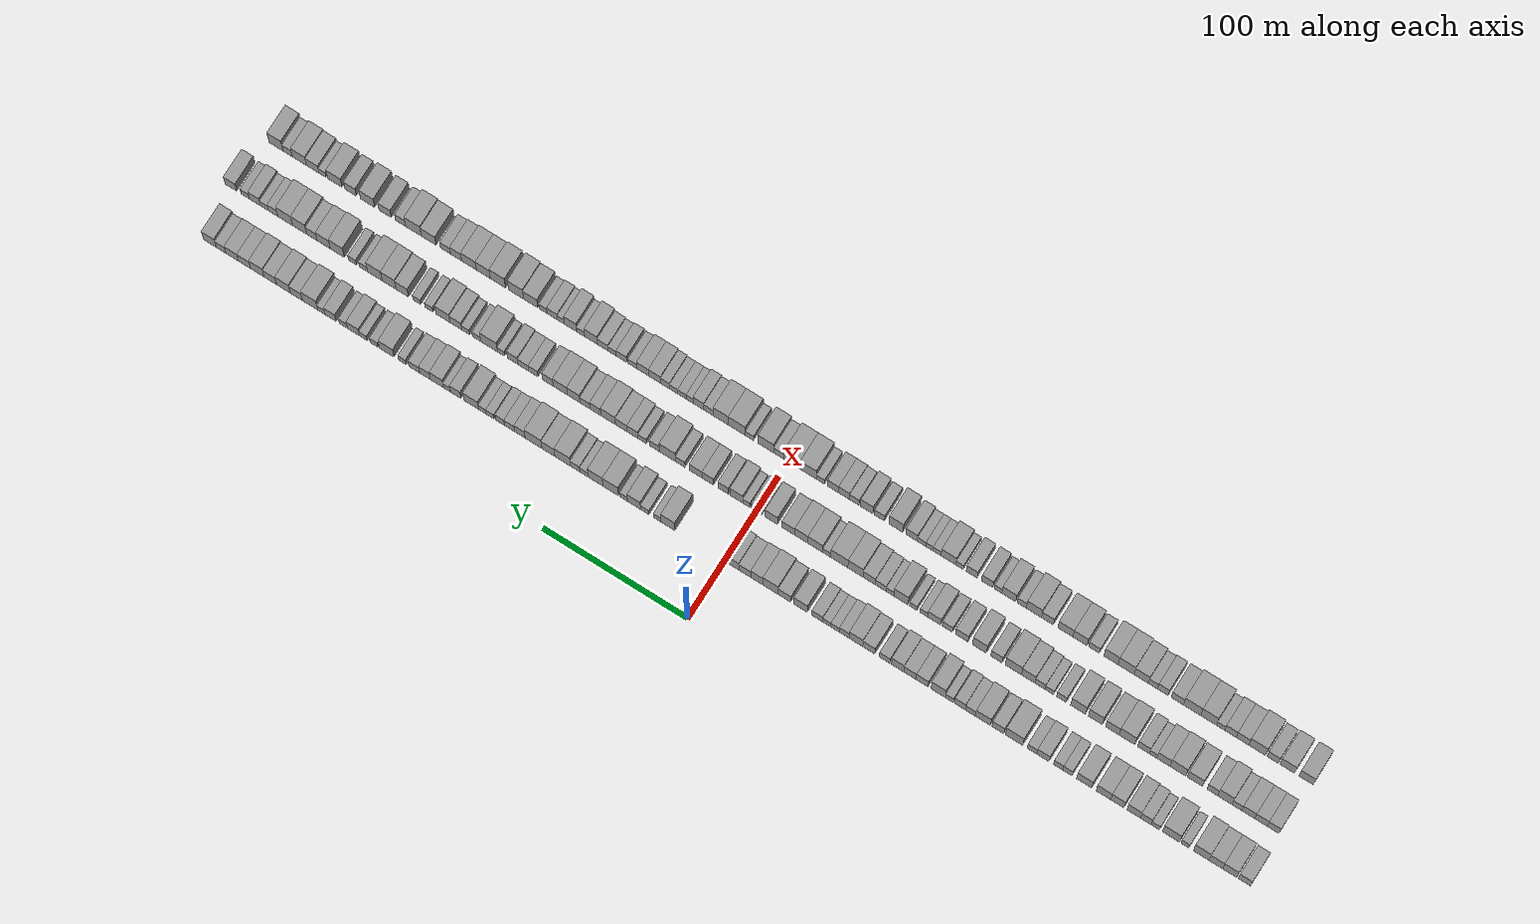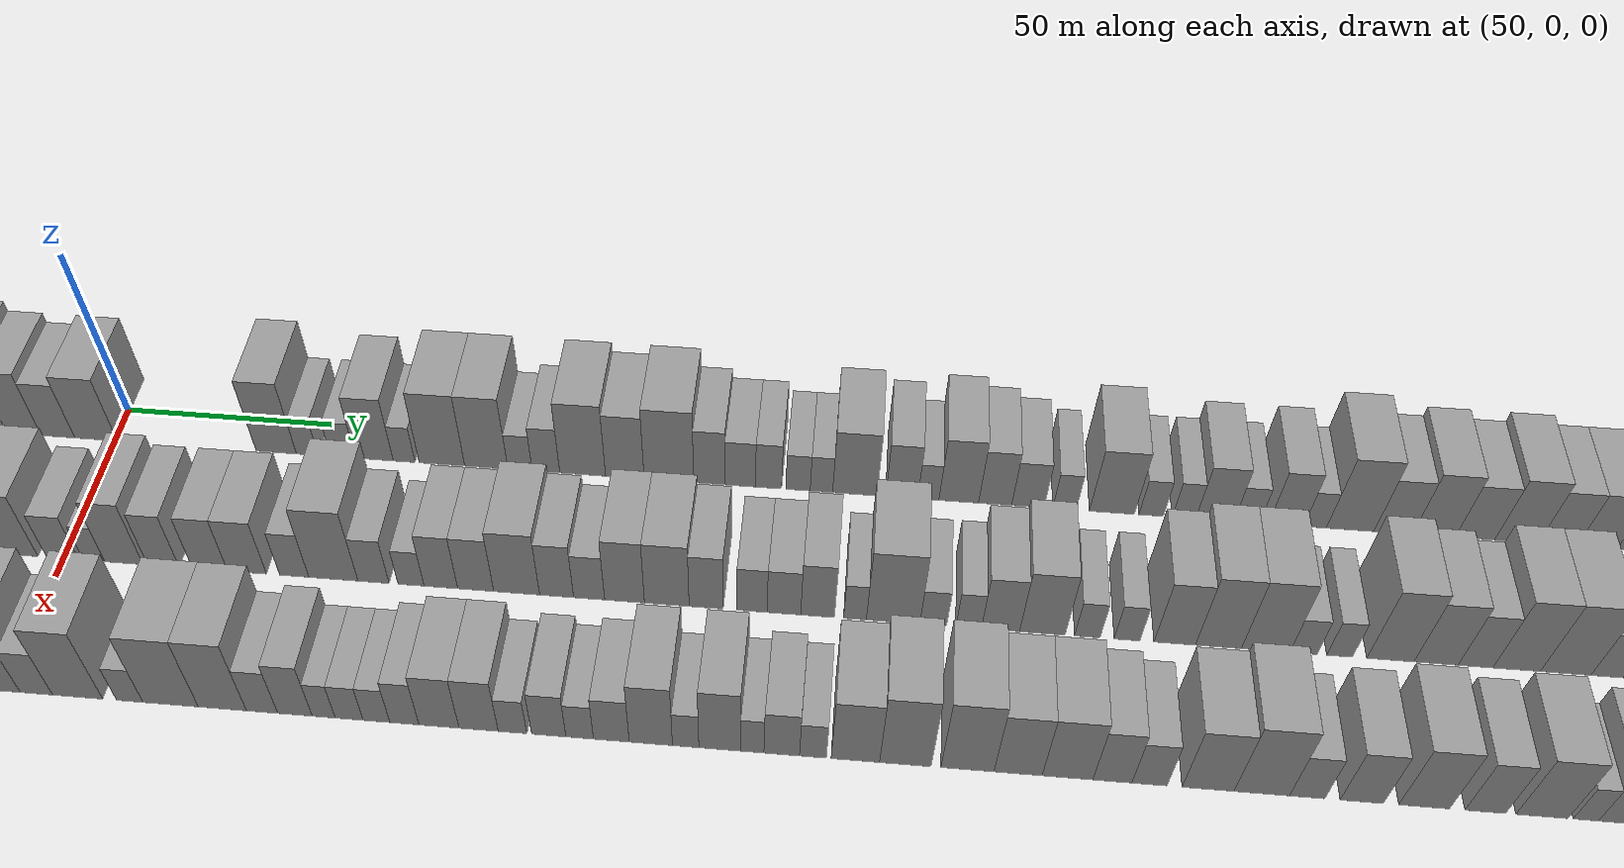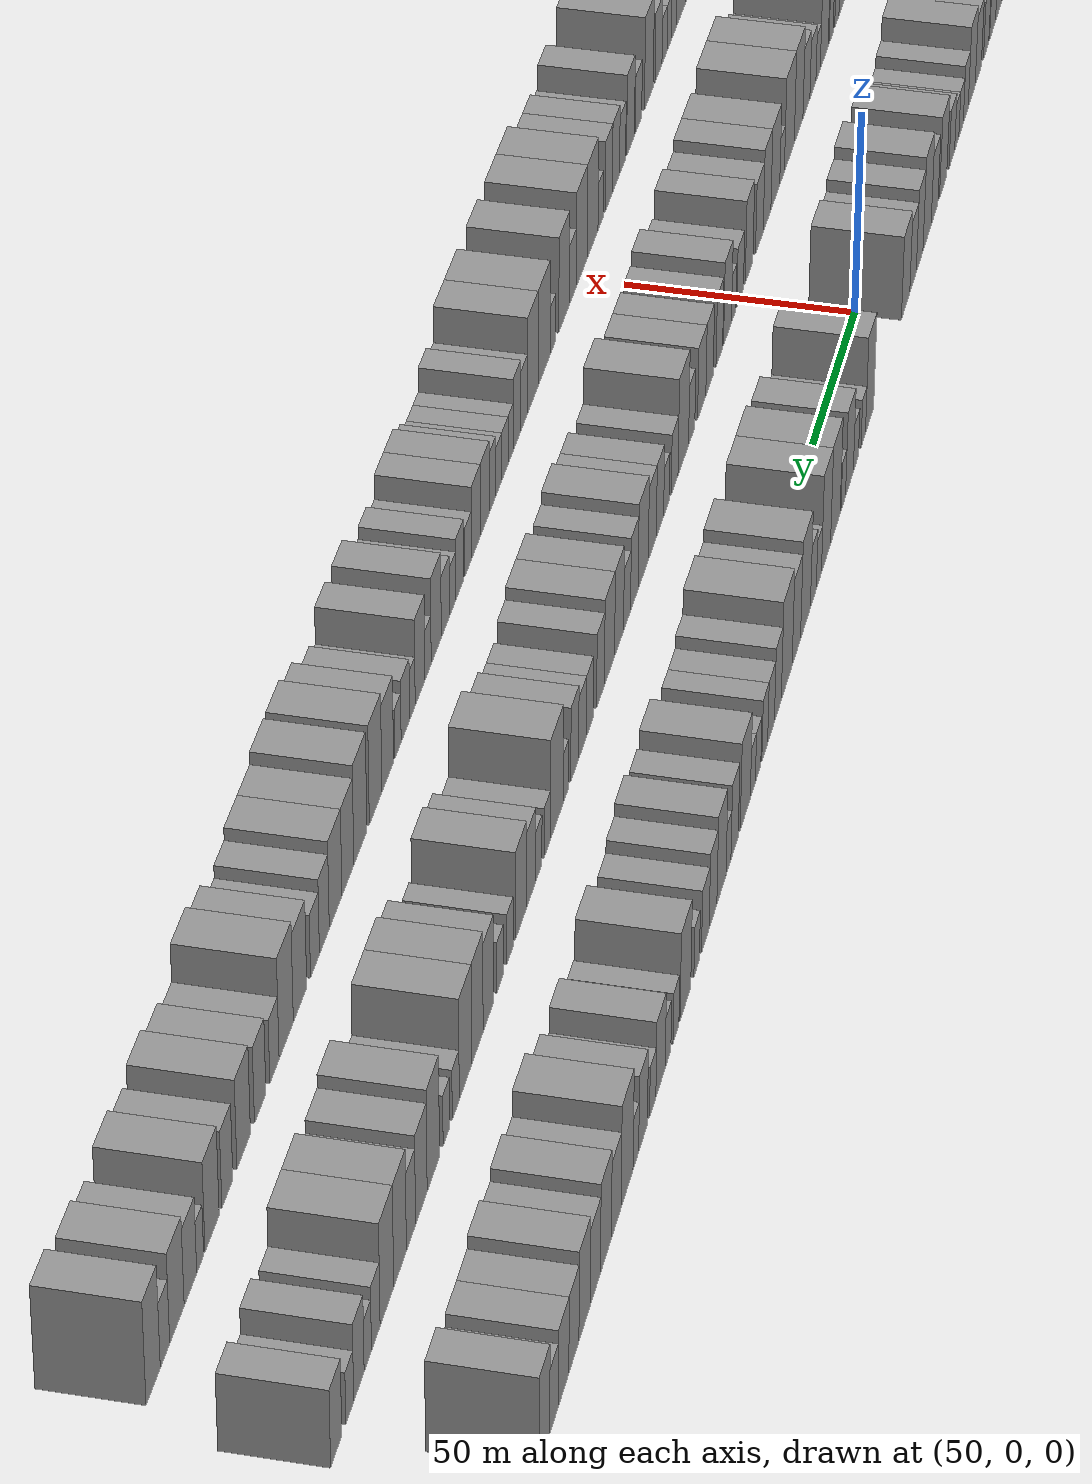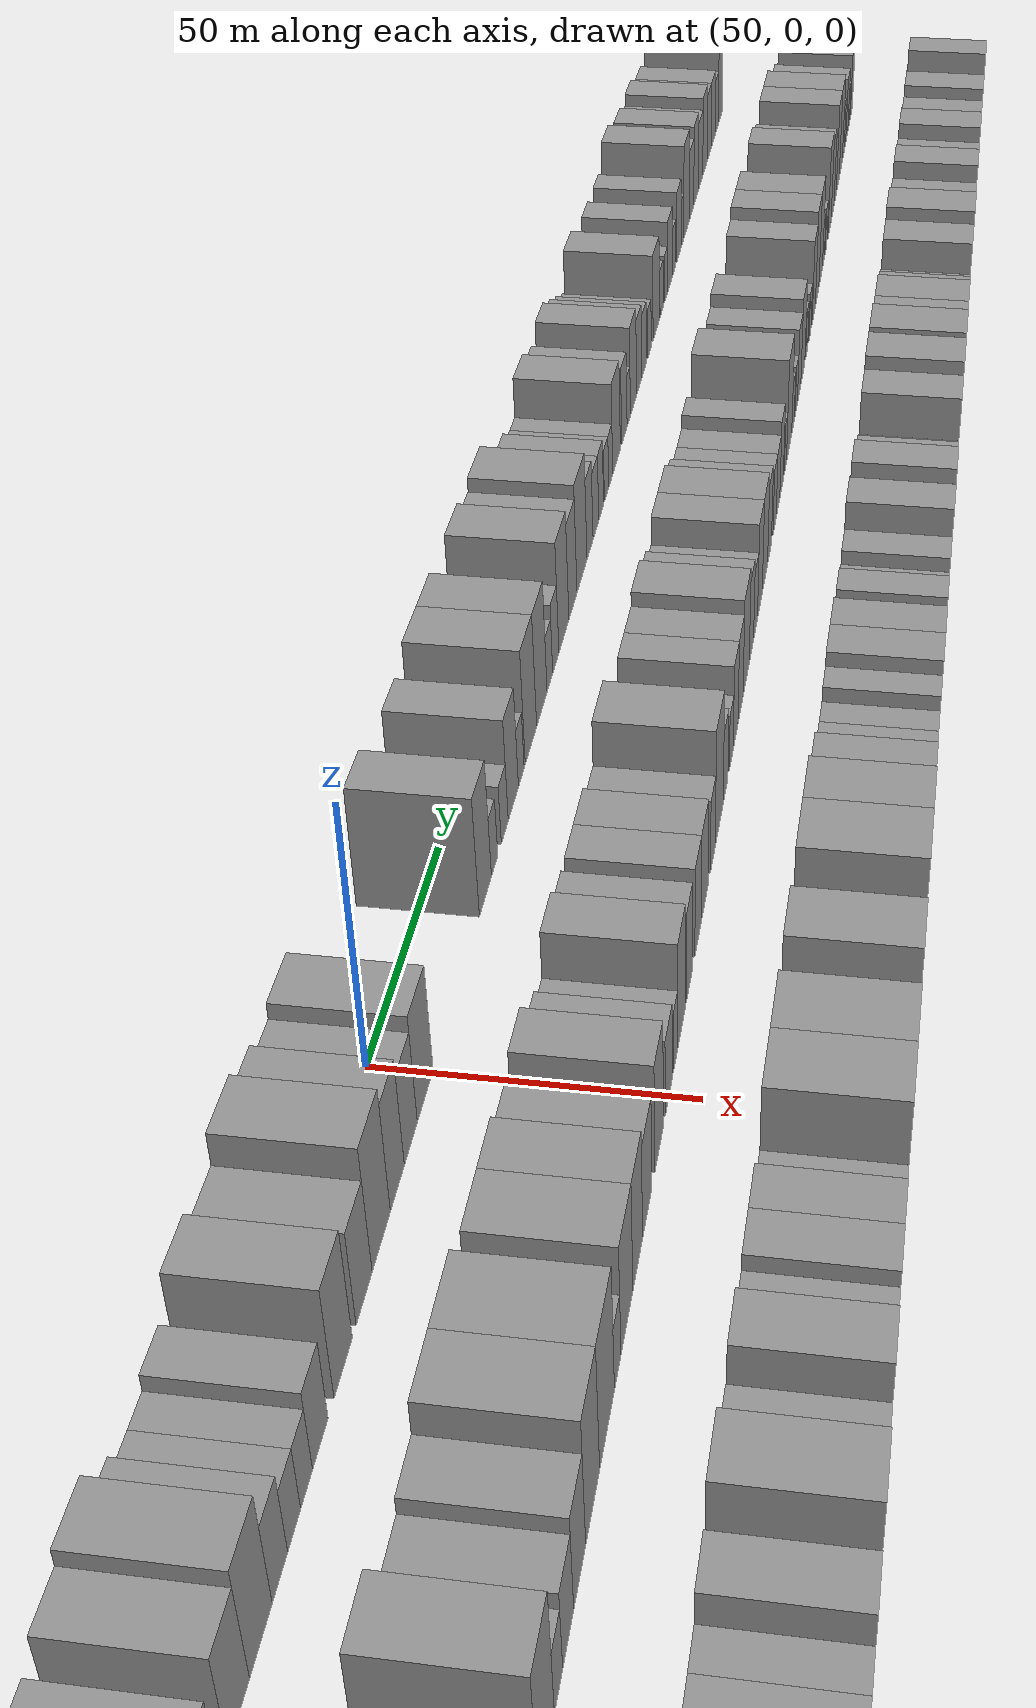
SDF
<sdf version="1.6">
 <world name="default">
  <scene>
   <sky><clouds><speed>12</speed></clouds></sky>
   <ambient>0.4 0.4 0.4 1</ambient>
   <background>0.7 0.7 0.7 1</background>
   <shadows>1</shadows>
  </scene>
  <gravity>0 0 -9.8066</gravity>
  <magnetic_field>6e-06 2.3e-05 -4.2e-05</magnetic_field>
  <physics default="0" name="default_physics" type="ode">
   <ode>
    <solver>
     <type>quick</type>
     <iters>10</iters>
     <sor>1.0</sor>
     <use_dynamic_moi_rescaling>0</use_dynamic_moi_rescaling>
    </solver>
    <constraints>
     <cfm>0</cfm>
     <erp>0.2</erp>
     <contact_max_correcting_vel>100</contact_max_correcting_vel>
     <contact_surface_layer>0.001</contact_surface_layer>
    </constraints>
   </ode>
   <max_step_size>0.004</max_step_size>
   <real_time_factor>1</real_time_factor>
   <real_time_update_rate>250</real_time_update_rate>
  </physics>
  <light name="sun" type="directional">
   <pose>0 0 10 0 0 0</pose>
   <diffuse>0.8 0.8 0.8 1</diffuse>
   <specular>0.2 0.2 0.2 1</specular>
   <attenuation>
    <range>1000</range>
    <constant>0.9</constant>
    <linear>0.01</linear>
    <quadratic>0.001</quadratic>
   </attenuation>
   <direction>-0.5 0.1 -0.9</direction>
  </light>
  <model name="building_1">
   <static>1</static>
   <pose>50.0000 -355.7815 0 0.000000 0.000000 0.000000</pose>
   <link name="link">
    <pose>0 0 9.00 0 0 0</pose>
    <collision name="collision"><geometry><box><size>20.0000 8.4371 18.0000</size></box></geometry></collision>
    <visual name="visual">
     <cast_shadows>0</cast_shadows>
     <geometry><box><size>20.0000 8.4371 18.0000</size></box></geometry>
     <material>
      <script>
       <uri>model://grey_wall/materials/scripts</uri>
       <uri>model://grey_wall/materials/textures</uri>
       <name>vrc/grey_wall</name>
      </script>
     </material>
    </visual>
   </link>
  </model>
  <model name="building_2">
   <static>1</static>
   <pose>50.0000 -345.7512 0 0.000000 0.000000 0.000000</pose>
   <link name="link">
    <pose>0 0 10.50 0 0 0</pose>
    <collision name="collision"><geometry><box><size>20.0000 9.6234 21.0000</size></box></geometry></collision>
    <visual name="visual">
     <cast_shadows>0</cast_shadows>
     <geometry><box><size>20.0000 9.6234 21.0000</size></box></geometry>
     <material>
      <script>
       <uri>model://grey_wall/materials/scripts</uri>
       <uri>model://grey_wall/materials/textures</uri>
       <name>vrc/grey_wall</name>
      </script>
     </material>
    </visual>
   </link>
  </model>
  <model name="building_3">
   <static>1</static>
   <pose>50.0000 -336.3448 0 0.000000 0.000000 0.000000</pose>
   <link name="link">
    <pose>0 0 10.50 0 0 0</pose>
    <collision name="collision"><geometry><box><size>20.0000 9.1895 21.0000</size></box></geometry></collision>
    <visual name="visual">
     <cast_shadows>0</cast_shadows>
     <geometry><box><size>20.0000 9.1895 21.0000</size></box></geometry>
     <material>
      <script>
       <uri>model://grey_wall/materials/scripts</uri>
       <uri>model://grey_wall/materials/textures</uri>
       <name>vrc/grey_wall</name>
      </script>
     </material>
    </visual>
   </link>
  </model>
  <model name="building_4">
   <static>1</static>
   <pose>50.0000 -326.4318 0 0.000000 0.000000 0.000000</pose>
   <link name="link">
    <pose>0 0 12.00 0 0 0</pose>
    <collision name="collision"><geometry><box><size>20.0000 10.6364 24.0000</size></box></geometry></collision>
    <visual name="visual">
     <cast_shadows>0</cast_shadows>
     <geometry><box><size>20.0000 10.6364 24.0000</size></box></geometry>
     <material>
      <script>
       <uri>model://grey_wall/materials/scripts</uri>
       <uri>model://grey_wall/materials/textures</uri>
       <name>vrc/grey_wall</name>
      </script>
     </material>
    </visual>
   </link>
  </model>
  <model name="building_5">
   <static>1</static>
   <pose>50.0000 -315.4185 0 0.000000 0.000000 0.000000</pose>
   <link name="link">
    <pose>0 0 6.00 0 0 0</pose>
    <collision name="collision"><geometry><box><size>20.0000 5.3902 12.0000</size></box></geometry></collision>
    <visual name="visual">
     <cast_shadows>0</cast_shadows>
     <geometry><box><size>20.0000 5.3902 12.0000</size></box></geometry>
     <material>
      <script>
       <uri>model://grey_wall/materials/scripts</uri>
       <uri>model://grey_wall/materials/textures</uri>
       <name>vrc/grey_wall</name>
      </script>
     </material>
    </visual>
   </link>
  </model>
  <model name="building_6">
   <static>1</static>
   <pose>50.0000 -305.8967 0 0.000000 0.000000 0.000000</pose>
   <link name="link">
    <pose>0 0 12.00 0 0 0</pose>
    <collision name="collision"><geometry><box><size>20.0000 11.6535 24.0000</size></box></geometry></collision>
    <visual name="visual">
     <cast_shadows>0</cast_shadows>
     <geometry><box><size>20.0000 11.6535 24.0000</size></box></geometry>
     <material>
      <script>
       <uri>model://grey_wall/materials/scripts</uri>
       <uri>model://grey_wall/materials/textures</uri>
       <name>vrc/grey_wall</name>
      </script>
     </material>
    </visual>
   </link>
  </model>
  <model name="building_7">
   <static>1</static>
   <pose>50.0000 -295.2478 0 0.000000 0.000000 0.000000</pose>
   <link name="link">
    <pose>0 0 6.00 0 0 0</pose>
    <collision name="collision"><geometry><box><size>20.0000 5.6443 12.0000</size></box></geometry></collision>
    <visual name="visual">
     <cast_shadows>0</cast_shadows>
     <geometry><box><size>20.0000 5.6443 12.0000</size></box></geometry>
     <material>
      <script>
       <uri>model://grey_wall/materials/scripts</uri>
       <uri>model://grey_wall/materials/textures</uri>
       <name>vrc/grey_wall</name>
      </script>
     </material>
    </visual>
   </link>
  </model>
  <model name="building_8">
   <static>1</static>
   <pose>50.0000 -288.7038 0 0.000000 0.000000 0.000000</pose>
   <link name="link">
    <pose>0 0 9.00 0 0 0</pose>
    <collision name="collision"><geometry><box><size>20.0000 7.4436 18.0000</size></box></geometry></collision>
    <visual name="visual">
     <cast_shadows>0</cast_shadows>
     <geometry><box><size>20.0000 7.4436 18.0000</size></box></geometry>
     <material>
      <script>
       <uri>model://grey_wall/materials/scripts</uri>
       <uri>model://grey_wall/materials/textures</uri>
       <name>vrc/grey_wall</name>
      </script>
     </material>
    </visual>
   </link>
  </model>
  <model name="building_9">
   <static>1</static>
   <pose>50.0000 -280.4125 0 0.000000 0.000000 0.000000</pose>
   <link name="link">
    <pose>0 0 10.50 0 0 0</pose>
    <collision name="collision"><geometry><box><size>20.0000 9.1390 21.0000</size></box></geometry></collision>
    <visual name="visual">
     <cast_shadows>0</cast_shadows>
     <geometry><box><size>20.0000 9.1390 21.0000</size></box></geometry>
     <material>
      <script>
       <uri>model://grey_wall/materials/scripts</uri>
       <uri>model://grey_wall/materials/textures</uri>
       <name>vrc/grey_wall</name>
      </script>
     </material>
    </visual>
   </link>
  </model>
  <model name="building_10">
   <static>1</static>
   <pose>50.0000 -269.3442 0 0.000000 0.000000 0.000000</pose>
   <link name="link">
    <pose>0 0 10.50 0 0 0</pose>
    <collision name="collision"><geometry><box><size>20.0000 8.9977 21.0000</size></box></geometry></collision>
    <visual name="visual">
     <cast_shadows>0</cast_shadows>
     <geometry><box><size>20.0000 8.9977 21.0000</size></box></geometry>
     <material>
      <script>
       <uri>model://grey_wall/materials/scripts</uri>
       <uri>model://grey_wall/materials/textures</uri>
       <name>vrc/grey_wall</name>
      </script>
     </material>
    </visual>
   </link>
  </model>
  <model name="building_11">
   <static>1</static>
   <pose>50.0000 -259.8650 0 0.000000 0.000000 0.000000</pose>
   <link name="link">
    <pose>0 0 10.50 0 0 0</pose>
    <collision name="collision"><geometry><box><size>20.0000 9.9606 21.0000</size></box></geometry></collision>
    <visual name="visual">
     <cast_shadows>0</cast_shadows>
     <geometry><box><size>20.0000 9.9606 21.0000</size></box></geometry>
     <material>
      <script>
       <uri>model://grey_wall/materials/scripts</uri>
       <uri>model://grey_wall/materials/textures</uri>
       <name>vrc/grey_wall</name>
      </script>
     </material>
    </visual>
   </link>
  </model>
  <model name="building_12">
   <static>1</static>
   <pose>50.0000 -246.6740 0 0.000000 0.000000 0.000000</pose>
   <link name="link">
    <pose>0 0 10.50 0 0 0</pose>
    <collision name="collision"><geometry><box><size>20.0000 10.4215 21.0000</size></box></geometry></collision>
    <visual name="visual">
     <cast_shadows>0</cast_shadows>
     <geometry><box><size>20.0000 10.4215 21.0000</size></box></geometry>
     <material>
      <script>
       <uri>model://grey_wall/materials/scripts</uri>
       <uri>model://grey_wall/materials/textures</uri>
       <name>vrc/grey_wall</name>
      </script>
     </material>
    </visual>
   </link>
  </model>
  <model name="building_13">
   <static>1</static>
   <pose>50.0000 -235.3233 0 0.000000 0.000000 0.000000</pose>
   <link name="link">
    <pose>0 0 7.50 0 0 0</pose>
    <collision name="collision"><geometry><box><size>20.0000 6.2798 15.0000</size></box></geometry></collision>
    <visual name="visual">
     <cast_shadows>0</cast_shadows>
     <geometry><box><size>20.0000 6.2798 15.0000</size></box></geometry>
     <material>
      <script>
       <uri>model://grey_wall/materials/scripts</uri>
       <uri>model://grey_wall/materials/textures</uri>
       <name>vrc/grey_wall</name>
      </script>
     </material>
    </visual>
   </link>
  </model>
  <model name="building_14">
   <static>1</static>
   <pose>50.0000 -228.9634 0 0.000000 0.000000 0.000000</pose>
   <link name="link">
    <pose>0 0 7.50 0 0 0</pose>
    <collision name="collision"><geometry><box><size>20.0000 6.4400 15.0000</size></box></geometry></collision>
    <visual name="visual">
     <cast_shadows>0</cast_shadows>
     <geometry><box><size>20.0000 6.4400 15.0000</size></box></geometry>
     <material>
      <script>
       <uri>model://grey_wall/materials/scripts</uri>
       <uri>model://grey_wall/materials/textures</uri>
       <name>vrc/grey_wall</name>
      </script>
     </material>
    </visual>
   </link>
  </model>
  <model name="building_15">
   <static>1</static>
   <pose>50.0000 -218.5569 0 0.000000 0.000000 0.000000</pose>
   <link name="link">
    <pose>0 0 9.00 0 0 0</pose>
    <collision name="collision"><geometry><box><size>20.0000 8.3730 18.0000</size></box></geometry></collision>
    <visual name="visual">
     <cast_shadows>0</cast_shadows>
     <geometry><box><size>20.0000 8.3730 18.0000</size></box></geometry>
     <material>
      <script>
       <uri>model://grey_wall/materials/scripts</uri>
       <uri>model://grey_wall/materials/textures</uri>
       <name>vrc/grey_wall</name>
      </script>
     </material>
    </visual>
   </link>
  </model>
  <model name="building_16">
   <static>1</static>
   <pose>50.0000 -211.0873 0 0.000000 0.000000 0.000000</pose>
   <link name="link">
    <pose>0 0 7.50 0 0 0</pose>
    <collision name="collision"><geometry><box><size>20.0000 6.5662 15.0000</size></box></geometry></collision>
    <visual name="visual">
     <cast_shadows>0</cast_shadows>
     <geometry><box><size>20.0000 6.5662 15.0000</size></box></geometry>
     <material>
      <script>
       <uri>model://grey_wall/materials/scripts</uri>
       <uri>model://grey_wall/materials/textures</uri>
       <name>vrc/grey_wall</name>
      </script>
     </material>
    </visual>
   </link>
  </model>
  <model name="building_17">
   <static>1</static>
   <pose>50.0000 -198.8618 0 0.000000 0.000000 0.000000</pose>
   <link name="link">
    <pose>0 0 12.00 0 0 0</pose>
    <collision name="collision"><geometry><box><size>20.0000 11.8849 24.0000</size></box></geometry></collision>
    <visual name="visual">
     <cast_shadows>0</cast_shadows>
     <geometry><box><size>20.0000 11.8849 24.0000</size></box></geometry>
     <material>
      <script>
       <uri>model://grey_wall/materials/scripts</uri>
       <uri>model://grey_wall/materials/textures</uri>
       <name>vrc/grey_wall</name>
      </script>
     </material>
    </visual>
   </link>
  </model>
  <model name="building_18">
   <static>1</static>
   <pose>50.0000 -187.7998 0 0.000000 0.000000 0.000000</pose>
   <link name="link">
    <pose>0 0 9.00 0 0 0</pose>
    <collision name="collision"><geometry><box><size>20.0000 8.2391 18.0000</size></box></geometry></collision>
    <visual name="visual">
     <cast_shadows>0</cast_shadows>
     <geometry><box><size>20.0000 8.2391 18.0000</size></box></geometry>
     <material>
      <script>
       <uri>model://grey_wall/materials/scripts</uri>
       <uri>model://grey_wall/materials/textures</uri>
       <name>vrc/grey_wall</name>
      </script>
     </material>
    </visual>
   </link>
  </model>
  <model name="building_19">
   <static>1</static>
   <pose>50.0000 -177.5316 0 0.000000 0.000000 0.000000</pose>
   <link name="link">
    <pose>0 0 10.50 0 0 0</pose>
    <collision name="collision"><geometry><box><size>20.0000 10.2972 21.0000</size></box></geometry></collision>
    <visual name="visual">
     <cast_shadows>0</cast_shadows>
     <geometry><box><size>20.0000 10.2972 21.0000</size></box></geometry>
     <material>
      <script>
       <uri>model://grey_wall/materials/scripts</uri>
       <uri>model://grey_wall/materials/textures</uri>
       <name>vrc/grey_wall</name>
      </script>
     </material>
    </visual>
   </link>
  </model>
  <model name="building_20">
   <static>1</static>
   <pose>50.0000 -168.8650 0 0.000000 0.000000 0.000000</pose>
   <link name="link">
    <pose>0 0 7.50 0 0 0</pose>
    <collision name="collision"><geometry><box><size>20.0000 7.0361 15.0000</size></box></geometry></collision>
    <visual name="visual">
     <cast_shadows>0</cast_shadows>
     <geometry><box><size>20.0000 7.0361 15.0000</size></box></geometry>
     <material>
      <script>
       <uri>model://grey_wall/materials/scripts</uri>
       <uri>model://grey_wall/materials/textures</uri>
       <name>vrc/grey_wall</name>
      </script>
     </material>
    </visual>
   </link>
  </model>
  <model name="building_21">
   <static>1</static>
   <pose>50.0000 -161.7235 0 0.000000 0.000000 0.000000</pose>
   <link name="link">
    <pose>0 0 9.00 0 0 0</pose>
    <collision name="collision"><geometry><box><size>20.0000 7.2469 18.0000</size></box></geometry></collision>
    <visual name="visual">
     <cast_shadows>0</cast_shadows>
     <geometry><box><size>20.0000 7.2469 18.0000</size></box></geometry>
     <material>
      <script>
       <uri>model://grey_wall/materials/scripts</uri>
       <uri>model://grey_wall/materials/textures</uri>
       <name>vrc/grey_wall</name>
      </script>
     </material>
    </visual>
   </link>
  </model>
  <model name="building_22">
   <static>1</static>
   <pose>50.0000 -154.3871 0 0.000000 0.000000 0.000000</pose>
   <link name="link">
    <pose>0 0 6.00 0 0 0</pose>
    <collision name="collision"><geometry><box><size>20.0000 5.4259 12.0000</size></box></geometry></collision>
    <visual name="visual">
     <cast_shadows>0</cast_shadows>
     <geometry><box><size>20.0000 5.4259 12.0000</size></box></geometry>
     <material>
      <script>
       <uri>model://grey_wall/materials/scripts</uri>
       <uri>model://grey_wall/materials/textures</uri>
       <name>vrc/grey_wall</name>
      </script>
     </material>
    </visual>
   </link>
  </model>
  <model name="building_23">
   <static>1</static>
   <pose>50.0000 -146.8042 0 0.000000 0.000000 0.000000</pose>
   <link name="link">
    <pose>0 0 12.00 0 0 0</pose>
    <collision name="collision"><geometry><box><size>20.0000 9.7397 24.0000</size></box></geometry></collision>
    <visual name="visual">
     <cast_shadows>0</cast_shadows>
     <geometry><box><size>20.0000 9.7397 24.0000</size></box></geometry>
     <material>
      <script>
       <uri>model://grey_wall/materials/scripts</uri>
       <uri>model://grey_wall/materials/textures</uri>
       <name>vrc/grey_wall</name>
      </script>
     </material>
    </visual>
   </link>
  </model>
  <model name="building_24">
   <static>1</static>
   <pose>50.0000 -135.8123 0 0.000000 0.000000 0.000000</pose>
   <link name="link">
    <pose>0 0 9.00 0 0 0</pose>
    <collision name="collision"><geometry><box><size>20.0000 8.2442 18.0000</size></box></geometry></collision>
    <visual name="visual">
     <cast_shadows>0</cast_shadows>
     <geometry><box><size>20.0000 8.2442 18.0000</size></box></geometry>
     <material>
      <script>
       <uri>model://grey_wall/materials/scripts</uri>
       <uri>model://grey_wall/materials/textures</uri>
       <name>vrc/grey_wall</name>
      </script>
     </material>
    </visual>
   </link>
  </model>
  <model name="building_25">
   <static>1</static>
   <pose>50.0000 -127.4321 0 0.000000 0.000000 0.000000</pose>
   <link name="link">
    <pose>0 0 9.00 0 0 0</pose>
    <collision name="collision"><geometry><box><size>20.0000 8.5163 18.0000</size></box></geometry></collision>
    <visual name="visual">
     <cast_shadows>0</cast_shadows>
     <geometry><box><size>20.0000 8.5163 18.0000</size></box></geometry>
     <material>
      <script>
       <uri>model://grey_wall/materials/scripts</uri>
       <uri>model://grey_wall/materials/textures</uri>
       <name>vrc/grey_wall</name>
      </script>
     </material>
    </visual>
   </link>
  </model>
  <model name="building_26">
   <static>1</static>
   <pose>50.0000 -118.9645 0 0.000000 0.000000 0.000000</pose>
   <link name="link">
    <pose>0 0 10.50 0 0 0</pose>
    <collision name="collision"><geometry><box><size>20.0000 8.4188 21.0000</size></box></geometry></collision>
    <visual name="visual">
     <cast_shadows>0</cast_shadows>
     <geometry><box><size>20.0000 8.4188 21.0000</size></box></geometry>
     <material>
      <script>
       <uri>model://grey_wall/materials/scripts</uri>
       <uri>model://grey_wall/materials/textures</uri>
       <name>vrc/grey_wall</name>
      </script>
     </material>
    </visual>
   </link>
  </model>
  <model name="building_27">
   <static>1</static>
   <pose>50.0000 -110.1095 0 0.000000 0.000000 0.000000</pose>
   <link name="link">
    <pose>0 0 7.50 0 0 0</pose>
    <collision name="collision"><geometry><box><size>20.0000 7.2914 15.0000</size></box></geometry></collision>
    <visual name="visual">
     <cast_shadows>0</cast_shadows>
     <geometry><box><size>20.0000 7.2914 15.0000</size></box></geometry>
     <material>
      <script>
       <uri>model://grey_wall/materials/scripts</uri>
       <uri>model://grey_wall/materials/textures</uri>
       <name>vrc/grey_wall</name>
      </script>
     </material>
    </visual>
   </link>
  </model>
  <model name="building_28">
   <static>1</static>
   <pose>50.0000 -99.2491 0 0.000000 0.000000 0.000000</pose>
   <link name="link">
    <pose>0 0 9.00 0 0 0</pose>
    <collision name="collision"><geometry><box><size>20.0000 8.4293 18.0000</size></box></geometry></collision>
    <visual name="visual">
     <cast_shadows>0</cast_shadows>
     <geometry><box><size>20.0000 8.4293 18.0000</size></box></geometry>
     <material>
      <script>
       <uri>model://grey_wall/materials/scripts</uri>
       <uri>model://grey_wall/materials/textures</uri>
       <name>vrc/grey_wall</name>
      </script>
     </material>
    </visual>
   </link>
  </model>
  <model name="building_29">
   <static>1</static>
   <pose>50.0000 -90.3243 0 0.000000 0.000000 0.000000</pose>
   <link name="link">
    <pose>0 0 10.50 0 0 0</pose>
    <collision name="collision"><geometry><box><size>20.0000 9.4204 21.0000</size></box></geometry></collision>
    <visual name="visual">
     <cast_shadows>0</cast_shadows>
     <geometry><box><size>20.0000 9.4204 21.0000</size></box></geometry>
     <material>
      <script>
       <uri>model://grey_wall/materials/scripts</uri>
       <uri>model://grey_wall/materials/textures</uri>
       <name>vrc/grey_wall</name>
      </script>
     </material>
    </visual>
   </link>
  </model>
  <model name="building_30">
   <static>1</static>
   <pose>50.0000 -82.2575 0 0.000000 0.000000 0.000000</pose>
   <link name="link">
    <pose>0 0 7.50 0 0 0</pose>
    <collision name="collision"><geometry><box><size>20.0000 6.7132 15.0000</size></box></geometry></collision>
    <visual name="visual">
     <cast_shadows>0</cast_shadows>
     <geometry><box><size>20.0000 6.7132 15.0000</size></box></geometry>
     <material>
      <script>
       <uri>model://grey_wall/materials/scripts</uri>
       <uri>model://grey_wall/materials/textures</uri>
       <name>vrc/grey_wall</name>
      </script>
     </material>
    </visual>
   </link>
  </model>
  <model name="building_31">
   <static>1</static>
   <pose>50.0000 -75.9709 0 0.000000 0.000000 0.000000</pose>
   <link name="link">
    <pose>0 0 6.00 0 0 0</pose>
    <collision name="collision"><geometry><box><size>20.0000 5.8601 12.0000</size></box></geometry></collision>
    <visual name="visual">
     <cast_shadows>0</cast_shadows>
     <geometry><box><size>20.0000 5.8601 12.0000</size></box></geometry>
     <material>
      <script>
       <uri>model://grey_wall/materials/scripts</uri>
       <uri>model://grey_wall/materials/textures</uri>
       <name>vrc/grey_wall</name>
      </script>
     </material>
    </visual>
   </link>
  </model>
  <model name="building_32">
   <static>1</static>
   <pose>50.0000 -70.2673 0 0.000000 0.000000 0.000000</pose>
   <link name="link">
    <pose>0 0 6.00 0 0 0</pose>
    <collision name="collision"><geometry><box><size>20.0000 5.5470 12.0000</size></box></geometry></collision>
    <visual name="visual">
     <cast_shadows>0</cast_shadows>
     <geometry><box><size>20.0000 5.5470 12.0000</size></box></geometry>
     <material>
      <script>
       <uri>model://grey_wall/materials/scripts</uri>
       <uri>model://grey_wall/materials/textures</uri>
       <name>vrc/grey_wall</name>
      </script>
     </material>
    </visual>
   </link>
  </model>
  <model name="building_33">
   <static>1</static>
   <pose>50.0000 -63.7525 0 0.000000 0.000000 0.000000</pose>
   <link name="link">
    <pose>0 0 7.50 0 0 0</pose>
    <collision name="collision"><geometry><box><size>20.0000 7.4826 15.0000</size></box></geometry></collision>
    <visual name="visual">
     <cast_shadows>0</cast_shadows>
     <geometry><box><size>20.0000 7.4826 15.0000</size></box></geometry>
     <material>
      <script>
       <uri>model://grey_wall/materials/scripts</uri>
       <uri>model://grey_wall/materials/textures</uri>
       <name>vrc/grey_wall</name>
      </script>
     </material>
    </visual>
   </link>
  </model>
  <model name="building_34">
   <static>1</static>
   <pose>50.0000 -52.3097 0 0.000000 0.000000 0.000000</pose>
   <link name="link">
    <pose>0 0 10.50 0 0 0</pose>
    <collision name="collision"><geometry><box><size>20.0000 9.4031 21.0000</size></box></geometry></collision>
    <visual name="visual">
     <cast_shadows>0</cast_shadows>
     <geometry><box><size>20.0000 9.4031 21.0000</size></box></geometry>
     <material>
      <script>
       <uri>model://grey_wall/materials/scripts</uri>
       <uri>model://grey_wall/materials/textures</uri>
       <name>vrc/grey_wall</name>
      </script>
     </material>
    </visual>
   </link>
  </model>
  <model name="building_35">
   <static>1</static>
   <pose>50.0000 -41.2139 0 0.000000 0.000000 0.000000</pose>
   <link name="link">
    <pose>0 0 9.00 0 0 0</pose>
    <collision name="collision"><geometry><box><size>20.0000 8.7885 18.0000</size></box></geometry></collision>
    <visual name="visual">
     <cast_shadows>0</cast_shadows>
     <geometry><box><size>20.0000 8.7885 18.0000</size></box></geometry>
     <material>
      <script>
       <uri>model://grey_wall/materials/scripts</uri>
       <uri>model://grey_wall/materials/textures</uri>
       <name>vrc/grey_wall</name>
      </script>
     </material>
    </visual>
   </link>
  </model>
  <model name="building_36">
   <static>1</static>
   <pose>50.0000 -31.5772 0 0.000000 0.000000 0.000000</pose>
   <link name="link">
    <pose>0 0 12.00 0 0 0</pose>
    <collision name="collision"><geometry><box><size>20.0000 10.4849 24.0000</size></box></geometry></collision>
    <visual name="visual">
     <cast_shadows>0</cast_shadows>
     <geometry><box><size>20.0000 10.4849 24.0000</size></box></geometry>
     <material>
      <script>
       <uri>model://grey_wall/materials/scripts</uri>
       <uri>model://grey_wall/materials/textures</uri>
       <name>vrc/grey_wall</name>
      </script>
     </material>
    </visual>
   </link>
  </model>
  <model name="building_37">
   <static>1</static>
   <pose>50.0000 -22.1295 0 0.000000 0.000000 0.000000</pose>
   <link name="link">
    <pose>0 0 10.50 0 0 0</pose>
    <collision name="collision"><geometry><box><size>20.0000 8.4103 21.0000</size></box></geometry></collision>
    <visual name="visual">
     <cast_shadows>0</cast_shadows>
     <geometry><box><size>20.0000 8.4103 21.0000</size></box></geometry>
     <material>
      <script>
       <uri>model://grey_wall/materials/scripts</uri>
       <uri>model://grey_wall/materials/textures</uri>
       <name>vrc/grey_wall</name>
      </script>
     </material>
    </visual>
   </link>
  </model>
  <model name="building_38">
   <static>1</static>
   <pose>50.0000 -13.8423 0 0.000000 0.000000 0.000000</pose>
   <link name="link">
    <pose>0 0 9.00 0 0 0</pose>
    <collision name="collision"><geometry><box><size>20.0000 8.1641 18.0000</size></box></geometry></collision>
    <visual name="visual">
     <cast_shadows>0</cast_shadows>
     <geometry><box><size>20.0000 8.1641 18.0000</size></box></geometry>
     <material>
      <script>
       <uri>model://grey_wall/materials/scripts</uri>
       <uri>model://grey_wall/materials/textures</uri>
       <name>vrc/grey_wall</name>
      </script>
     </material>
    </visual>
   </link>
  </model>
  <model name="building_39">
   <static>1</static>
   <pose>50.0000 -4.5751 0 0.000000 0.000000 0.000000</pose>
   <link name="link">
    <pose>0 0 10.50 0 0 0</pose>
    <collision name="collision"><geometry><box><size>20.0000 10.3705 21.0000</size></box></geometry></collision>
    <visual name="visual">
     <cast_shadows>0</cast_shadows>
     <geometry><box><size>20.0000 10.3705 21.0000</size></box></geometry>
     <material>
      <script>
       <uri>model://grey_wall/materials/scripts</uri>
       <uri>model://grey_wall/materials/textures</uri>
       <name>vrc/grey_wall</name>
      </script>
     </material>
    </visual>
   </link>
  </model>
  <model name="building_40">
   <static>1</static>
   <pose>50.0000 39.1611 0 0.000000 0.000000 0.000000</pose>
   <link name="link">
    <pose>0 0 12.00 0 0 0</pose>
    <collision name="collision"><geometry><box><size>20.0000 9.7006 24.0000</size></box></geometry></collision>
    <visual name="visual">
     <cast_shadows>0</cast_shadows>
     <geometry><box><size>20.0000 9.7006 24.0000</size></box></geometry>
     <material>
      <script>
       <uri>model://grey_wall/materials/scripts</uri>
       <uri>model://grey_wall/materials/textures</uri>
       <name>vrc/grey_wall</name>
      </script>
     </material>
    </visual>
   </link>
  </model>
  <model name="building_41">
   <static>1</static>
   <pose>50.0000 46.6222 0 0.000000 0.000000 0.000000</pose>
   <link name="link">
    <pose>0 0 6.00 0 0 0</pose>
    <collision name="collision"><geometry><box><size>20.0000 5.2216 12.0000</size></box></geometry></collision>
    <visual name="visual">
     <cast_shadows>0</cast_shadows>
     <geometry><box><size>20.0000 5.2216 12.0000</size></box></geometry>
     <material>
      <script>
       <uri>model://grey_wall/materials/scripts</uri>
       <uri>model://grey_wall/materials/textures</uri>
       <name>vrc/grey_wall</name>
      </script>
     </material>
    </visual>
   </link>
  </model>
  <model name="building_42">
   <static>1</static>
   <pose>50.0000 55.2175 0 0.000000 0.000000 0.000000</pose>
   <link name="link">
    <pose>0 0 6.00 0 0 0</pose>
    <collision name="collision"><geometry><box><size>20.0000 5.9689 12.0000</size></box></geometry></collision>
    <visual name="visual">
     <cast_shadows>0</cast_shadows>
     <geometry><box><size>20.0000 5.9689 12.0000</size></box></geometry>
     <material>
      <script>
       <uri>model://grey_wall/materials/scripts</uri>
       <uri>model://grey_wall/materials/textures</uri>
       <name>vrc/grey_wall</name>
      </script>
     </material>
    </visual>
   </link>
  </model>
  <model name="building_43">
   <static>1</static>
   <pose>50.0000 62.7230 0 0.000000 0.000000 0.000000</pose>
   <link name="link">
    <pose>0 0 10.50 0 0 0</pose>
    <collision name="collision"><geometry><box><size>20.0000 9.0422 21.0000</size></box></geometry></collision>
    <visual name="visual">
     <cast_shadows>0</cast_shadows>
     <geometry><box><size>20.0000 9.0422 21.0000</size></box></geometry>
     <material>
      <script>
       <uri>model://grey_wall/materials/scripts</uri>
       <uri>model://grey_wall/materials/textures</uri>
       <name>vrc/grey_wall</name>
      </script>
     </material>
    </visual>
   </link>
  </model>
  <model name="building_44">
   <static>1</static>
   <pose>50.0000 69.8419 0 0.000000 0.000000 0.000000</pose>
   <link name="link">
    <pose>0 0 6.00 0 0 0</pose>
    <collision name="collision"><geometry><box><size>20.0000 5.1956 12.0000</size></box></geometry></collision>
    <visual name="visual">
     <cast_shadows>0</cast_shadows>
     <geometry><box><size>20.0000 5.1956 12.0000</size></box></geometry>
     <material>
      <script>
       <uri>model://grey_wall/materials/scripts</uri>
       <uri>model://grey_wall/materials/textures</uri>
       <name>vrc/grey_wall</name>
      </script>
     </material>
    </visual>
   </link>
  </model>
  <model name="building_45">
   <static>1</static>
   <pose>50.0000 78.8561 0 0.000000 0.000000 0.000000</pose>
   <link name="link">
    <pose>0 0 12.00 0 0 0</pose>
    <collision name="collision"><geometry><box><size>20.0000 10.8327 24.0000</size></box></geometry></collision>
    <visual name="visual">
     <cast_shadows>0</cast_shadows>
     <geometry><box><size>20.0000 10.8327 24.0000</size></box></geometry>
     <material>
      <script>
       <uri>model://grey_wall/materials/scripts</uri>
       <uri>model://grey_wall/materials/textures</uri>
       <name>vrc/grey_wall</name>
      </script>
     </material>
    </visual>
   </link>
  </model>
  <model name="building_46">
   <static>1</static>
   <pose>50.0000 89.3941 0 0.000000 0.000000 0.000000</pose>
   <link name="link">
    <pose>0 0 12.00 0 0 0</pose>
    <collision name="collision"><geometry><box><size>20.0000 10.2433 24.0000</size></box></geometry></collision>
    <visual name="visual">
     <cast_shadows>0</cast_shadows>
     <geometry><box><size>20.0000 10.2433 24.0000</size></box></geometry>
     <material>
      <script>
       <uri>model://grey_wall/materials/scripts</uri>
       <uri>model://grey_wall/materials/textures</uri>
       <name>vrc/grey_wall</name>
      </script>
     </material>
    </visual>
   </link>
  </model>
  <model name="building_47">
   <static>1</static>
   <pose>50.0000 97.3932 0 0.000000 0.000000 0.000000</pose>
   <link name="link">
    <pose>0 0 6.00 0 0 0</pose>
    <collision name="collision"><geometry><box><size>20.0000 5.7550 12.0000</size></box></geometry></collision>
    <visual name="visual">
     <cast_shadows>0</cast_shadows>
     <geometry><box><size>20.0000 5.7550 12.0000</size></box></geometry>
     <material>
      <script>
       <uri>model://grey_wall/materials/scripts</uri>
       <uri>model://grey_wall/materials/textures</uri>
       <name>vrc/grey_wall</name>
      </script>
     </material>
    </visual>
   </link>
  </model>
  <model name="building_48">
   <static>1</static>
   <pose>50.0000 103.5259 0 0.000000 0.000000 0.000000</pose>
   <link name="link">
    <pose>0 0 7.50 0 0 0</pose>
    <collision name="collision"><geometry><box><size>20.0000 6.5104 15.0000</size></box></geometry></collision>
    <visual name="visual">
     <cast_shadows>0</cast_shadows>
     <geometry><box><size>20.0000 6.5104 15.0000</size></box></geometry>
     <material>
      <script>
       <uri>model://grey_wall/materials/scripts</uri>
       <uri>model://grey_wall/materials/textures</uri>
       <name>vrc/grey_wall</name>
      </script>
     </material>
    </visual>
   </link>
  </model>
  <model name="building_49">
   <static>1</static>
   <pose>50.0000 112.1810 0 0.000000 0.000000 0.000000</pose>
   <link name="link">
    <pose>0 0 12.00 0 0 0</pose>
    <collision name="collision"><geometry><box><size>20.0000 10.7998 24.0000</size></box></geometry></collision>
    <visual name="visual">
     <cast_shadows>0</cast_shadows>
     <geometry><box><size>20.0000 10.7998 24.0000</size></box></geometry>
     <material>
      <script>
       <uri>model://grey_wall/materials/scripts</uri>
       <uri>model://grey_wall/materials/textures</uri>
       <name>vrc/grey_wall</name>
      </script>
     </material>
    </visual>
   </link>
  </model>
  <model name="building_50">
   <static>1</static>
   <pose>50.0000 122.1033 0 0.000000 0.000000 0.000000</pose>
   <link name="link">
    <pose>0 0 10.50 0 0 0</pose>
    <collision name="collision"><geometry><box><size>20.0000 9.0449 21.0000</size></box></geometry></collision>
    <visual name="visual">
     <cast_shadows>0</cast_shadows>
     <geometry><box><size>20.0000 9.0449 21.0000</size></box></geometry>
     <material>
      <script>
       <uri>model://grey_wall/materials/scripts</uri>
       <uri>model://grey_wall/materials/textures</uri>
       <name>vrc/grey_wall</name>
      </script>
     </material>
    </visual>
   </link>
  </model>
  <model name="building_51">
   <static>1</static>
   <pose>50.0000 132.4402 0 0.000000 0.000000 0.000000</pose>
   <link name="link">
    <pose>0 0 12.00 0 0 0</pose>
    <collision name="collision"><geometry><box><size>20.0000 11.6288 24.0000</size></box></geometry></collision>
    <visual name="visual">
     <cast_shadows>0</cast_shadows>
     <geometry><box><size>20.0000 11.6288 24.0000</size></box></geometry>
     <material>
      <script>
       <uri>model://grey_wall/materials/scripts</uri>
       <uri>model://grey_wall/materials/textures</uri>
       <name>vrc/grey_wall</name>
      </script>
     </material>
    </visual>
   </link>
  </model>
  <model name="building_52">
   <static>1</static>
   <pose>50.0000 141.8896 0 0.000000 0.000000 0.000000</pose>
   <link name="link">
    <pose>0 0 9.00 0 0 0</pose>
    <collision name="collision"><geometry><box><size>20.0000 7.2701 18.0000</size></box></geometry></collision>
    <visual name="visual">
     <cast_shadows>0</cast_shadows>
     <geometry><box><size>20.0000 7.2701 18.0000</size></box></geometry>
     <material>
      <script>
       <uri>model://grey_wall/materials/scripts</uri>
       <uri>model://grey_wall/materials/textures</uri>
       <name>vrc/grey_wall</name>
      </script>
     </material>
    </visual>
   </link>
  </model>
  <model name="building_53">
   <static>1</static>
   <pose>50.0000 149.0812 0 0.000000 0.000000 0.000000</pose>
   <link name="link">
    <pose>0 0 7.50 0 0 0</pose>
    <collision name="collision"><geometry><box><size>20.0000 7.1130 15.0000</size></box></geometry></collision>
    <visual name="visual">
     <cast_shadows>0</cast_shadows>
     <geometry><box><size>20.0000 7.1130 15.0000</size></box></geometry>
     <material>
      <script>
       <uri>model://grey_wall/materials/scripts</uri>
       <uri>model://grey_wall/materials/textures</uri>
       <name>vrc/grey_wall</name>
      </script>
     </material>
    </visual>
   </link>
  </model>
  <model name="building_54">
   <static>1</static>
   <pose>50.0000 155.6776 0 0.000000 0.000000 0.000000</pose>
   <link name="link">
    <pose>0 0 7.50 0 0 0</pose>
    <collision name="collision"><geometry><box><size>20.0000 6.0799 15.0000</size></box></geometry></collision>
    <visual name="visual">
     <cast_shadows>0</cast_shadows>
     <geometry><box><size>20.0000 6.0799 15.0000</size></box></geometry>
     <material>
      <script>
       <uri>model://grey_wall/materials/scripts</uri>
       <uri>model://grey_wall/materials/textures</uri>
       <name>vrc/grey_wall</name>
      </script>
     </material>
    </visual>
   </link>
  </model>
  <model name="building_55">
   <static>1</static>
   <pose>50.0000 162.5369 0 0.000000 0.000000 0.000000</pose>
   <link name="link">
    <pose>0 0 6.00 0 0 0</pose>
    <collision name="collision"><geometry><box><size>20.0000 5.6387 12.0000</size></box></geometry></collision>
    <visual name="visual">
     <cast_shadows>0</cast_shadows>
     <geometry><box><size>20.0000 5.6387 12.0000</size></box></geometry>
     <material>
      <script>
       <uri>model://grey_wall/materials/scripts</uri>
       <uri>model://grey_wall/materials/textures</uri>
       <name>vrc/grey_wall</name>
      </script>
     </material>
    </visual>
   </link>
  </model>
  <model name="building_56">
   <static>1</static>
   <pose>50.0000 167.9550 0 0.000000 0.000000 0.000000</pose>
   <link name="link">
    <pose>0 0 6.00 0 0 0</pose>
    <collision name="collision"><geometry><box><size>20.0000 5.1975 12.0000</size></box></geometry></collision>
    <visual name="visual">
     <cast_shadows>0</cast_shadows>
     <geometry><box><size>20.0000 5.1975 12.0000</size></box></geometry>
     <material>
      <script>
       <uri>model://grey_wall/materials/scripts</uri>
       <uri>model://grey_wall/materials/textures</uri>
       <name>vrc/grey_wall</name>
      </script>
     </material>
    </visual>
   </link>
  </model>
  <model name="building_57">
   <static>1</static>
   <pose>50.0000 175.6868 0 0.000000 0.000000 0.000000</pose>
   <link name="link">
    <pose>0 0 10.50 0 0 0</pose>
    <collision name="collision"><geometry><box><size>20.0000 10.2662 21.0000</size></box></geometry></collision>
    <visual name="visual">
     <cast_shadows>0</cast_shadows>
     <geometry><box><size>20.0000 10.2662 21.0000</size></box></geometry>
     <material>
      <script>
       <uri>model://grey_wall/materials/scripts</uri>
       <uri>model://grey_wall/materials/textures</uri>
       <name>vrc/grey_wall</name>
      </script>
     </material>
    </visual>
   </link>
  </model>
  <model name="building_58">
   <static>1</static>
   <pose>50.0000 186.5079 0 0.000000 0.000000 0.000000</pose>
   <link name="link">
    <pose>0 0 9.00 0 0 0</pose>
    <collision name="collision"><geometry><box><size>20.0000 7.3760 18.0000</size></box></geometry></collision>
    <visual name="visual">
     <cast_shadows>0</cast_shadows>
     <geometry><box><size>20.0000 7.3760 18.0000</size></box></geometry>
     <material>
      <script>
       <uri>model://grey_wall/materials/scripts</uri>
       <uri>model://grey_wall/materials/textures</uri>
       <name>vrc/grey_wall</name>
      </script>
     </material>
    </visual>
   </link>
  </model>
  <model name="building_59">
   <static>1</static>
   <pose>50.0000 192.6315 0 0.000000 0.000000 0.000000</pose>
   <link name="link">
    <pose>0 0 6.00 0 0 0</pose>
    <collision name="collision"><geometry><box><size>20.0000 4.8712 12.0000</size></box></geometry></collision>
    <visual name="visual">
     <cast_shadows>0</cast_shadows>
     <geometry><box><size>20.0000 4.8712 12.0000</size></box></geometry>
     <material>
      <script>
       <uri>model://grey_wall/materials/scripts</uri>
       <uri>model://grey_wall/materials/textures</uri>
       <name>vrc/grey_wall</name>
      </script>
     </material>
    </visual>
   </link>
  </model>
  <model name="building_60">
   <static>1</static>
   <pose>50.0000 199.6078 0 0.000000 0.000000 0.000000</pose>
   <link name="link">
    <pose>0 0 10.50 0 0 0</pose>
    <collision name="collision"><geometry><box><size>20.0000 9.0813 21.0000</size></box></geometry></collision>
    <visual name="visual">
     <cast_shadows>0</cast_shadows>
     <geometry><box><size>20.0000 9.0813 21.0000</size></box></geometry>
     <material>
      <script>
       <uri>model://grey_wall/materials/scripts</uri>
       <uri>model://grey_wall/materials/textures</uri>
       <name>vrc/grey_wall</name>
      </script>
     </material>
    </visual>
   </link>
  </model>
  <model name="building_61">
   <static>1</static>
   <pose>50.0000 207.9370 0 0.000000 0.000000 0.000000</pose>
   <link name="link">
    <pose>0 0 9.00 0 0 0</pose>
    <collision name="collision"><geometry><box><size>20.0000 7.5772 18.0000</size></box></geometry></collision>
    <visual name="visual">
     <cast_shadows>0</cast_shadows>
     <geometry><box><size>20.0000 7.5772 18.0000</size></box></geometry>
     <material>
      <script>
       <uri>model://grey_wall/materials/scripts</uri>
       <uri>model://grey_wall/materials/textures</uri>
       <name>vrc/grey_wall</name>
      </script>
     </material>
    </visual>
   </link>
  </model>
  <model name="building_62">
   <static>1</static>
   <pose>50.0000 215.4291 0 0.000000 0.000000 0.000000</pose>
   <link name="link">
    <pose>0 0 7.50 0 0 0</pose>
    <collision name="collision"><geometry><box><size>20.0000 7.4069 15.0000</size></box></geometry></collision>
    <visual name="visual">
     <cast_shadows>0</cast_shadows>
     <geometry><box><size>20.0000 7.4069 15.0000</size></box></geometry>
     <material>
      <script>
       <uri>model://grey_wall/materials/scripts</uri>
       <uri>model://grey_wall/materials/textures</uri>
       <name>vrc/grey_wall</name>
      </script>
     </material>
    </visual>
   </link>
  </model>
  <model name="building_63">
   <static>1</static>
   <pose>50.0000 223.8043 0 0.000000 0.000000 0.000000</pose>
   <link name="link">
    <pose>0 0 6.00 0 0 0</pose>
    <collision name="collision"><geometry><box><size>20.0000 5.3436 12.0000</size></box></geometry></collision>
    <visual name="visual">
     <cast_shadows>0</cast_shadows>
     <geometry><box><size>20.0000 5.3436 12.0000</size></box></geometry>
     <material>
      <script>
       <uri>model://grey_wall/materials/scripts</uri>
       <uri>model://grey_wall/materials/textures</uri>
       <name>vrc/grey_wall</name>
      </script>
     </material>
    </visual>
   </link>
  </model>
  <model name="building_64">
   <static>1</static>
   <pose>50.0000 234.6009 0 0.000000 0.000000 0.000000</pose>
   <link name="link">
    <pose>0 0 10.50 0 0 0</pose>
    <collision name="collision"><geometry><box><size>20.0000 10.2496 21.0000</size></box></geometry></collision>
    <visual name="visual">
     <cast_shadows>0</cast_shadows>
     <geometry><box><size>20.0000 10.2496 21.0000</size></box></geometry>
     <material>
      <script>
       <uri>model://grey_wall/materials/scripts</uri>
       <uri>model://grey_wall/materials/textures</uri>
       <name>vrc/grey_wall</name>
      </script>
     </material>
    </visual>
   </link>
  </model>
  <model name="building_65">
   <static>1</static>
   <pose>50.0000 243.4923 0 0.000000 0.000000 0.000000</pose>
   <link name="link">
    <pose>0 0 6.00 0 0 0</pose>
    <collision name="collision"><geometry><box><size>20.0000 5.5330 12.0000</size></box></geometry></collision>
    <visual name="visual">
     <cast_shadows>0</cast_shadows>
     <geometry><box><size>20.0000 5.5330 12.0000</size></box></geometry>
     <material>
      <script>
       <uri>model://grey_wall/materials/scripts</uri>
       <uri>model://grey_wall/materials/textures</uri>
       <name>vrc/grey_wall</name>
      </script>
     </material>
    </visual>
   </link>
  </model>
  <model name="building_66">
   <static>1</static>
   <pose>50.0000 250.9036 0 0.000000 0.000000 0.000000</pose>
   <link name="link">
    <pose>0 0 6.00 0 0 0</pose>
    <collision name="collision"><geometry><box><size>20.0000 5.2895 12.0000</size></box></geometry></collision>
    <visual name="visual">
     <cast_shadows>0</cast_shadows>
     <geometry><box><size>20.0000 5.2895 12.0000</size></box></geometry>
     <material>
      <script>
       <uri>model://grey_wall/materials/scripts</uri>
       <uri>model://grey_wall/materials/textures</uri>
       <name>vrc/grey_wall</name>
      </script>
     </material>
    </visual>
   </link>
  </model>
  <model name="building_67">
   <static>1</static>
   <pose>50.0000 257.8606 0 0.000000 0.000000 0.000000</pose>
   <link name="link">
    <pose>0 0 9.00 0 0 0</pose>
    <collision name="collision"><geometry><box><size>20.0000 8.6245 18.0000</size></box></geometry></collision>
    <visual name="visual">
     <cast_shadows>0</cast_shadows>
     <geometry><box><size>20.0000 8.6245 18.0000</size></box></geometry>
     <material>
      <script>
       <uri>model://grey_wall/materials/scripts</uri>
       <uri>model://grey_wall/materials/textures</uri>
       <name>vrc/grey_wall</name>
      </script>
     </material>
    </visual>
   </link>
  </model>
  <model name="building_68">
   <static>1</static>
   <pose>50.0000 265.0523 0 0.000000 0.000000 0.000000</pose>
   <link name="link">
    <pose>0 0 6.00 0 0 0</pose>
    <collision name="collision"><geometry><box><size>20.0000 5.7588 12.0000</size></box></geometry></collision>
    <visual name="visual">
     <cast_shadows>0</cast_shadows>
     <geometry><box><size>20.0000 5.7588 12.0000</size></box></geometry>
     <material>
      <script>
       <uri>model://grey_wall/materials/scripts</uri>
       <uri>model://grey_wall/materials/textures</uri>
       <name>vrc/grey_wall</name>
      </script>
     </material>
    </visual>
   </link>
  </model>
  <model name="building_69">
   <static>1</static>
   <pose>50.0000 273.8693 0 0.000000 0.000000 0.000000</pose>
   <link name="link">
    <pose>0 0 9.00 0 0 0</pose>
    <collision name="collision"><geometry><box><size>20.0000 7.8752 18.0000</size></box></geometry></collision>
    <visual name="visual">
     <cast_shadows>0</cast_shadows>
     <geometry><box><size>20.0000 7.8752 18.0000</size></box></geometry>
     <material>
      <script>
       <uri>model://grey_wall/materials/scripts</uri>
       <uri>model://grey_wall/materials/textures</uri>
       <name>vrc/grey_wall</name>
      </script>
     </material>
    </visual>
   </link>
  </model>
  <model name="building_70">
   <static>1</static>
   <pose>50.0000 280.3489 0 0.000000 0.000000 0.000000</pose>
   <link name="link">
    <pose>0 0 6.00 0 0 0</pose>
    <collision name="collision"><geometry><box><size>20.0000 5.0842 12.0000</size></box></geometry></collision>
    <visual name="visual">
     <cast_shadows>0</cast_shadows>
     <geometry><box><size>20.0000 5.0842 12.0000</size></box></geometry>
     <material>
      <script>
       <uri>model://grey_wall/materials/scripts</uri>
       <uri>model://grey_wall/materials/textures</uri>
       <name>vrc/grey_wall</name>
      </script>
     </material>
    </visual>
   </link>
  </model>
  <model name="building_71">
   <static>1</static>
   <pose>50.0000 288.2163 0 0.000000 0.000000 0.000000</pose>
   <link name="link">
    <pose>0 0 12.00 0 0 0</pose>
    <collision name="collision"><geometry><box><size>20.0000 10.6506 24.0000</size></box></geometry></collision>
    <visual name="visual">
     <cast_shadows>0</cast_shadows>
     <geometry><box><size>20.0000 10.6506 24.0000</size></box></geometry>
     <material>
      <script>
       <uri>model://grey_wall/materials/scripts</uri>
       <uri>model://grey_wall/materials/textures</uri>
       <name>vrc/grey_wall</name>
      </script>
     </material>
    </visual>
   </link>
  </model>
  <model name="building_72">
   <static>1</static>
   <pose>50.0000 297.8118 0 0.000000 0.000000 0.000000</pose>
   <link name="link">
    <pose>0 0 9.00 0 0 0</pose>
    <collision name="collision"><geometry><box><size>20.0000 8.5405 18.0000</size></box></geometry></collision>
    <visual name="visual">
     <cast_shadows>0</cast_shadows>
     <geometry><box><size>20.0000 8.5405 18.0000</size></box></geometry>
     <material>
      <script>
       <uri>model://grey_wall/materials/scripts</uri>
       <uri>model://grey_wall/materials/textures</uri>
       <name>vrc/grey_wall</name>
      </script>
     </material>
    </visual>
   </link>
  </model>
  <model name="building_73">
   <static>1</static>
   <pose>50.0000 306.8316 0 0.000000 0.000000 0.000000</pose>
   <link name="link">
    <pose>0 0 10.50 0 0 0</pose>
    <collision name="collision"><geometry><box><size>20.0000 9.4990 21.0000</size></box></geometry></collision>
    <visual name="visual">
     <cast_shadows>0</cast_shadows>
     <geometry><box><size>20.0000 9.4990 21.0000</size></box></geometry>
     <material>
      <script>
       <uri>model://grey_wall/materials/scripts</uri>
       <uri>model://grey_wall/materials/textures</uri>
       <name>vrc/grey_wall</name>
      </script>
     </material>
    </visual>
   </link>
  </model>
  <model name="building_74">
   <static>1</static>
   <pose>50.0000 315.9491 0 0.000000 0.000000 0.000000</pose>
   <link name="link">
    <pose>0 0 9.00 0 0 0</pose>
    <collision name="collision"><geometry><box><size>20.0000 8.7359 18.0000</size></box></geometry></collision>
    <visual name="visual">
     <cast_shadows>0</cast_shadows>
     <geometry><box><size>20.0000 8.7359 18.0000</size></box></geometry>
     <material>
      <script>
       <uri>model://grey_wall/materials/scripts</uri>
       <uri>model://grey_wall/materials/textures</uri>
       <name>vrc/grey_wall</name>
      </script>
     </material>
    </visual>
   </link>
  </model>
  <model name="building_75">
   <static>1</static>
   <pose>50.0000 325.1176 0 0.000000 0.000000 0.000000</pose>
   <link name="link">
    <pose>0 0 10.50 0 0 0</pose>
    <collision name="collision"><geometry><box><size>20.0000 9.6011 21.0000</size></box></geometry></collision>
    <visual name="visual">
     <cast_shadows>0</cast_shadows>
     <geometry><box><size>20.0000 9.6011 21.0000</size></box></geometry>
     <material>
      <script>
       <uri>model://grey_wall/materials/scripts</uri>
       <uri>model://grey_wall/materials/textures</uri>
       <name>vrc/grey_wall</name>
      </script>
     </material>
    </visual>
   </link>
  </model>
  <model name="building_76">
   <static>1</static>
   <pose>50.0000 334.1489 0 0.000000 0.000000 0.000000</pose>
   <link name="link">
    <pose>0 0 9.00 0 0 0</pose>
    <collision name="collision"><geometry><box><size>20.0000 8.4615 18.0000</size></box></geometry></collision>
    <visual name="visual">
     <cast_shadows>0</cast_shadows>
     <geometry><box><size>20.0000 8.4615 18.0000</size></box></geometry>
     <material>
      <script>
       <uri>model://grey_wall/materials/scripts</uri>
       <uri>model://grey_wall/materials/textures</uri>
       <name>vrc/grey_wall</name>
      </script>
     </material>
    </visual>
   </link>
  </model>
  <model name="building_77">
   <static>1</static>
   <pose>50.0000 342.8352 0 0.000000 0.000000 0.000000</pose>
   <link name="link">
    <pose>0 0 9.00 0 0 0</pose>
    <collision name="collision"><geometry><box><size>20.0000 8.9112 18.0000</size></box></geometry></collision>
    <visual name="visual">
     <cast_shadows>0</cast_shadows>
     <geometry><box><size>20.0000 8.9112 18.0000</size></box></geometry>
     <material>
      <script>
       <uri>model://grey_wall/materials/scripts</uri>
       <uri>model://grey_wall/materials/textures</uri>
       <name>vrc/grey_wall</name>
      </script>
     </material>
    </visual>
   </link>
  </model>
  <model name="building_78">
   <static>1</static>
   <pose>50.0000 350.7238 0 0.000000 0.000000 0.000000</pose>
   <link name="link">
    <pose>0 0 7.50 0 0 0</pose>
    <collision name="collision"><geometry><box><size>20.0000 6.8660 15.0000</size></box></geometry></collision>
    <visual name="visual">
     <cast_shadows>0</cast_shadows>
     <geometry><box><size>20.0000 6.8660 15.0000</size></box></geometry>
     <material>
      <script>
       <uri>model://grey_wall/materials/scripts</uri>
       <uri>model://grey_wall/materials/textures</uri>
       <name>vrc/grey_wall</name>
      </script>
     </material>
    </visual>
   </link>
  </model>
  <model name="building_79">
   <static>1</static>
   <pose>50.0000 358.5395 0 0.000000 0.000000 0.000000</pose>
   <link name="link">
    <pose>0 0 10.50 0 0 0</pose>
    <collision name="collision"><geometry><box><size>20.0000 8.7655 21.0000</size></box></geometry></collision>
    <visual name="visual">
     <cast_shadows>0</cast_shadows>
     <geometry><box><size>20.0000 8.7655 21.0000</size></box></geometry>
     <material>
      <script>
       <uri>model://grey_wall/materials/scripts</uri>
       <uri>model://grey_wall/materials/textures</uri>
       <name>vrc/grey_wall</name>
      </script>
     </material>
    </visual>
   </link>
  </model>
  <model name="building_80">
   <static>1</static>
   <pose>85.0000 -353.9408 0 0.000000 0.000000 0.000000</pose>
   <link name="link">
    <pose>0 0 9.00 0 0 0</pose>
    <collision name="collision"><geometry><box><size>20.0000 8.1183 18.0000</size></box></geometry></collision>
    <visual name="visual">
     <cast_shadows>0</cast_shadows>
     <geometry><box><size>20.0000 8.1183 18.0000</size></box></geometry>
     <material>
      <script>
       <uri>model://grey_wall/materials/scripts</uri>
       <uri>model://grey_wall/materials/textures</uri>
       <name>vrc/grey_wall</name>
      </script>
     </material>
    </visual>
   </link>
  </model>
  <model name="building_81">
   <static>1</static>
   <pose>85.0000 -345.6753 0 0.000000 0.000000 0.000000</pose>
   <link name="link">
    <pose>0 0 9.00 0 0 0</pose>
    <collision name="collision"><geometry><box><size>20.0000 8.4128 18.0000</size></box></geometry></collision>
    <visual name="visual">
     <cast_shadows>0</cast_shadows>
     <geometry><box><size>20.0000 8.4128 18.0000</size></box></geometry>
     <material>
      <script>
       <uri>model://grey_wall/materials/scripts</uri>
       <uri>model://grey_wall/materials/textures</uri>
       <name>vrc/grey_wall</name>
      </script>
     </material>
    </visual>
   </link>
  </model>
  <model name="building_82">
   <static>1</static>
   <pose>85.0000 -337.0203 0 0.000000 0.000000 0.000000</pose>
   <link name="link">
    <pose>0 0 9.00 0 0 0</pose>
    <collision name="collision"><geometry><box><size>20.0000 8.8972 18.0000</size></box></geometry></collision>
    <visual name="visual">
     <cast_shadows>0</cast_shadows>
     <geometry><box><size>20.0000 8.8972 18.0000</size></box></geometry>
     <material>
      <script>
       <uri>model://grey_wall/materials/scripts</uri>
       <uri>model://grey_wall/materials/textures</uri>
       <name>vrc/grey_wall</name>
      </script>
     </material>
    </visual>
   </link>
  </model>
  <model name="building_83">
   <static>1</static>
   <pose>85.0000 -329.3189 0 0.000000 0.000000 0.000000</pose>
   <link name="link">
    <pose>0 0 7.50 0 0 0</pose>
    <collision name="collision"><geometry><box><size>20.0000 6.5057 15.0000</size></box></geometry></collision>
    <visual name="visual">
     <cast_shadows>0</cast_shadows>
     <geometry><box><size>20.0000 6.5057 15.0000</size></box></geometry>
     <material>
      <script>
       <uri>model://grey_wall/materials/scripts</uri>
       <uri>model://grey_wall/materials/textures</uri>
       <name>vrc/grey_wall</name>
      </script>
     </material>
    </visual>
   </link>
  </model>
  <model name="building_84">
   <static>1</static>
   <pose>85.0000 -321.1531 0 0.000000 0.000000 0.000000</pose>
   <link name="link">
    <pose>0 0 12.00 0 0 0</pose>
    <collision name="collision"><geometry><box><size>20.0000 9.8258 24.0000</size></box></geometry></collision>
    <visual name="visual">
     <cast_shadows>0</cast_shadows>
     <geometry><box><size>20.0000 9.8258 24.0000</size></box></geometry>
     <material>
      <script>
       <uri>model://grey_wall/materials/scripts</uri>
       <uri>model://grey_wall/materials/textures</uri>
       <name>vrc/grey_wall</name>
      </script>
     </material>
    </visual>
   </link>
  </model>
  <model name="building_85">
   <static>1</static>
   <pose>85.0000 -312.5501 0 0.000000 0.000000 0.000000</pose>
   <link name="link">
    <pose>0 0 9.00 0 0 0</pose>
    <collision name="collision"><geometry><box><size>20.0000 7.3802 18.0000</size></box></geometry></collision>
    <visual name="visual">
     <cast_shadows>0</cast_shadows>
     <geometry><box><size>20.0000 7.3802 18.0000</size></box></geometry>
     <material>
      <script>
       <uri>model://grey_wall/materials/scripts</uri>
       <uri>model://grey_wall/materials/textures</uri>
       <name>vrc/grey_wall</name>
      </script>
     </material>
    </visual>
   </link>
  </model>
  <model name="building_86">
   <static>1</static>
   <pose>85.0000 -300.7098 0 0.000000 0.000000 0.000000</pose>
   <link name="link">
    <pose>0 0 10.50 0 0 0</pose>
    <collision name="collision"><geometry><box><size>20.0000 10.3003 21.0000</size></box></geometry></collision>
    <visual name="visual">
     <cast_shadows>0</cast_shadows>
     <geometry><box><size>20.0000 10.3003 21.0000</size></box></geometry>
     <material>
      <script>
       <uri>model://grey_wall/materials/scripts</uri>
       <uri>model://grey_wall/materials/textures</uri>
       <name>vrc/grey_wall</name>
      </script>
     </material>
    </visual>
   </link>
  </model>
  <model name="building_87">
   <static>1</static>
   <pose>85.0000 -289.2352 0 0.000000 0.000000 0.000000</pose>
   <link name="link">
    <pose>0 0 12.00 0 0 0</pose>
    <collision name="collision"><geometry><box><size>20.0000 10.6489 24.0000</size></box></geometry></collision>
    <visual name="visual">
     <cast_shadows>0</cast_shadows>
     <geometry><box><size>20.0000 10.6489 24.0000</size></box></geometry>
     <material>
      <script>
       <uri>model://grey_wall/materials/scripts</uri>
       <uri>model://grey_wall/materials/textures</uri>
       <name>vrc/grey_wall</name>
      </script>
     </material>
    </visual>
   </link>
  </model>
  <model name="building_88">
   <static>1</static>
   <pose>85.0000 -279.3035 0 0.000000 0.000000 0.000000</pose>
   <link name="link">
    <pose>0 0 10.50 0 0 0</pose>
    <collision name="collision"><geometry><box><size>20.0000 9.2144 21.0000</size></box></geometry></collision>
    <visual name="visual">
     <cast_shadows>0</cast_shadows>
     <geometry><box><size>20.0000 9.2144 21.0000</size></box></geometry>
     <material>
      <script>
       <uri>model://grey_wall/materials/scripts</uri>
       <uri>model://grey_wall/materials/textures</uri>
       <name>vrc/grey_wall</name>
      </script>
     </material>
    </visual>
   </link>
  </model>
  <model name="building_89">
   <static>1</static>
   <pose>85.0000 -272.1898 0 0.000000 0.000000 0.000000</pose>
   <link name="link">
    <pose>0 0 6.00 0 0 0</pose>
    <collision name="collision"><geometry><box><size>20.0000 5.0131 12.0000</size></box></geometry></collision>
    <visual name="visual">
     <cast_shadows>0</cast_shadows>
     <geometry><box><size>20.0000 5.0131 12.0000</size></box></geometry>
     <material>
      <script>
       <uri>model://grey_wall/materials/scripts</uri>
       <uri>model://grey_wall/materials/textures</uri>
       <name>vrc/grey_wall</name>
      </script>
     </material>
    </visual>
   </link>
  </model>
  <model name="building_90">
   <static>1</static>
   <pose>85.0000 -265.7035 0 0.000000 0.000000 0.000000</pose>
   <link name="link">
    <pose>0 0 9.00 0 0 0</pose>
    <collision name="collision"><geometry><box><size>20.0000 7.9597 18.0000</size></box></geometry></collision>
    <visual name="visual">
     <cast_shadows>0</cast_shadows>
     <geometry><box><size>20.0000 7.9597 18.0000</size></box></geometry>
     <material>
      <script>
       <uri>model://grey_wall/materials/scripts</uri>
       <uri>model://grey_wall/materials/textures</uri>
       <name>vrc/grey_wall</name>
      </script>
     </material>
    </visual>
   </link>
  </model>
  <model name="building_91">
   <static>1</static>
   <pose>85.0000 -254.3781 0 0.000000 0.000000 0.000000</pose>
   <link name="link">
    <pose>0 0 12.00 0 0 0</pose>
    <collision name="collision"><geometry><box><size>20.0000 10.6911 24.0000</size></box></geometry></collision>
    <visual name="visual">
     <cast_shadows>0</cast_shadows>
     <geometry><box><size>20.0000 10.6911 24.0000</size></box></geometry>
     <material>
      <script>
       <uri>model://grey_wall/materials/scripts</uri>
       <uri>model://grey_wall/materials/textures</uri>
       <name>vrc/grey_wall</name>
      </script>
     </material>
    </visual>
   </link>
  </model>
  <model name="building_92">
   <static>1</static>
   <pose>85.0000 -244.3536 0 0.000000 0.000000 0.000000</pose>
   <link name="link">
    <pose>0 0 10.50 0 0 0</pose>
    <collision name="collision"><geometry><box><size>20.0000 9.3578 21.0000</size></box></geometry></collision>
    <visual name="visual">
     <cast_shadows>0</cast_shadows>
     <geometry><box><size>20.0000 9.3578 21.0000</size></box></geometry>
     <material>
      <script>
       <uri>model://grey_wall/materials/scripts</uri>
       <uri>model://grey_wall/materials/textures</uri>
       <name>vrc/grey_wall</name>
      </script>
     </material>
    </visual>
   </link>
  </model>
  <model name="building_93">
   <static>1</static>
   <pose>85.0000 -232.8557 0 0.000000 0.000000 0.000000</pose>
   <link name="link">
    <pose>0 0 12.00 0 0 0</pose>
    <collision name="collision"><geometry><box><size>20.0000 9.6380 24.0000</size></box></geometry></collision>
    <visual name="visual">
     <cast_shadows>0</cast_shadows>
     <geometry><box><size>20.0000 9.6380 24.0000</size></box></geometry>
     <material>
      <script>
       <uri>model://grey_wall/materials/scripts</uri>
       <uri>model://grey_wall/materials/textures</uri>
       <name>vrc/grey_wall</name>
      </script>
     </material>
    </visual>
   </link>
  </model>
  <model name="building_94">
   <static>1</static>
   <pose>85.0000 -220.9613 0 0.000000 0.000000 0.000000</pose>
   <link name="link">
    <pose>0 0 12.00 0 0 0</pose>
    <collision name="collision"><geometry><box><size>20.0000 10.1509 24.0000</size></box></geometry></collision>
    <visual name="visual">
     <cast_shadows>0</cast_shadows>
     <geometry><box><size>20.0000 10.1509 24.0000</size></box></geometry>
     <material>
      <script>
       <uri>model://grey_wall/materials/scripts</uri>
       <uri>model://grey_wall/materials/textures</uri>
       <name>vrc/grey_wall</name>
      </script>
     </material>
    </visual>
   </link>
  </model>
  <model name="building_95">
   <static>1</static>
   <pose>85.0000 -209.5859 0 0.000000 0.000000 0.000000</pose>
   <link name="link">
    <pose>0 0 7.50 0 0 0</pose>
    <collision name="collision"><geometry><box><size>20.0000 6.6000 15.0000</size></box></geometry></collision>
    <visual name="visual">
     <cast_shadows>0</cast_shadows>
     <geometry><box><size>20.0000 6.6000 15.0000</size></box></geometry>
     <material>
      <script>
       <uri>model://grey_wall/materials/scripts</uri>
       <uri>model://grey_wall/materials/textures</uri>
       <name>vrc/grey_wall</name>
      </script>
     </material>
    </visual>
   </link>
  </model>
  <model name="building_96">
   <static>1</static>
   <pose>85.0000 -201.3395 0 0.000000 0.000000 0.000000</pose>
   <link name="link">
    <pose>0 0 6.00 0 0 0</pose>
    <collision name="collision"><geometry><box><size>20.0000 5.8927 12.0000</size></box></geometry></collision>
    <visual name="visual">
     <cast_shadows>0</cast_shadows>
     <geometry><box><size>20.0000 5.8927 12.0000</size></box></geometry>
     <material>
      <script>
       <uri>model://grey_wall/materials/scripts</uri>
       <uri>model://grey_wall/materials/textures</uri>
       <name>vrc/grey_wall</name>
      </script>
     </material>
    </visual>
   </link>
  </model>
  <model name="building_97">
   <static>1</static>
   <pose>85.0000 -194.9258 0 0.000000 0.000000 0.000000</pose>
   <link name="link">
    <pose>0 0 7.50 0 0 0</pose>
    <collision name="collision"><geometry><box><size>20.0000 6.9347 15.0000</size></box></geometry></collision>
    <visual name="visual">
     <cast_shadows>0</cast_shadows>
     <geometry><box><size>20.0000 6.9347 15.0000</size></box></geometry>
     <material>
      <script>
       <uri>model://grey_wall/materials/scripts</uri>
       <uri>model://grey_wall/materials/textures</uri>
       <name>vrc/grey_wall</name>
      </script>
     </material>
    </visual>
   </link>
  </model>
  <model name="building_98">
   <static>1</static>
   <pose>85.0000 -186.8367 0 0.000000 0.000000 0.000000</pose>
   <link name="link">
    <pose>0 0 10.50 0 0 0</pose>
    <collision name="collision"><geometry><box><size>20.0000 9.2436 21.0000</size></box></geometry></collision>
    <visual name="visual">
     <cast_shadows>0</cast_shadows>
     <geometry><box><size>20.0000 9.2436 21.0000</size></box></geometry>
     <material>
      <script>
       <uri>model://grey_wall/materials/scripts</uri>
       <uri>model://grey_wall/materials/textures</uri>
       <name>vrc/grey_wall</name>
      </script>
     </material>
    </visual>
   </link>
  </model>
  <model name="building_99">
   <static>1</static>
   <pose>85.0000 -176.6480 0 0.000000 0.000000 0.000000</pose>
   <link name="link">
    <pose>0 0 12.00 0 0 0</pose>
    <collision name="collision"><geometry><box><size>20.0000 11.1337 24.0000</size></box></geometry></collision>
    <visual name="visual">
     <cast_shadows>0</cast_shadows>
     <geometry><box><size>20.0000 11.1337 24.0000</size></box></geometry>
     <material>
      <script>
       <uri>model://grey_wall/materials/scripts</uri>
       <uri>model://grey_wall/materials/textures</uri>
       <name>vrc/grey_wall</name>
      </script>
     </material>
    </visual>
   </link>
  </model>
  <model name="building_100">
   <static>1</static>
   <pose>85.0000 -165.1414 0 0.000000 0.000000 0.000000</pose>
   <link name="link">
    <pose>0 0 9.00 0 0 0</pose>
    <collision name="collision"><geometry><box><size>20.0000 7.8794 18.0000</size></box></geometry></collision>
    <visual name="visual">
     <cast_shadows>0</cast_shadows>
     <geometry><box><size>20.0000 7.8794 18.0000</size></box></geometry>
     <material>
      <script>
       <uri>model://grey_wall/materials/scripts</uri>
       <uri>model://grey_wall/materials/textures</uri>
       <name>vrc/grey_wall</name>
      </script>
     </material>
    </visual>
   </link>
  </model>
  <model name="building_101">
   <static>1</static>
   <pose>85.0000 -153.3951 0 0.000000 0.000000 0.000000</pose>
   <link name="link">
    <pose>0 0 12.00 0 0 0</pose>
    <collision name="collision"><geometry><box><size>20.0000 9.6133 24.0000</size></box></geometry></collision>
    <visual name="visual">
     <cast_shadows>0</cast_shadows>
     <geometry><box><size>20.0000 9.6133 24.0000</size></box></geometry>
     <material>
      <script>
       <uri>model://grey_wall/materials/scripts</uri>
       <uri>model://grey_wall/materials/textures</uri>
       <name>vrc/grey_wall</name>
      </script>
     </material>
    </visual>
   </link>
  </model>
  <model name="building_102">
   <static>1</static>
   <pose>85.0000 -141.3218 0 0.000000 0.000000 0.000000</pose>
   <link name="link">
    <pose>0 0 9.00 0 0 0</pose>
    <collision name="collision"><geometry><box><size>20.0000 8.5334 18.0000</size></box></geometry></collision>
    <visual name="visual">
     <cast_shadows>0</cast_shadows>
     <geometry><box><size>20.0000 8.5334 18.0000</size></box></geometry>
     <material>
      <script>
       <uri>model://grey_wall/materials/scripts</uri>
       <uri>model://grey_wall/materials/textures</uri>
       <name>vrc/grey_wall</name>
      </script>
     </material>
    </visual>
   </link>
  </model>
  <model name="building_103">
   <static>1</static>
   <pose>85.0000 -131.4717 0 0.000000 0.000000 0.000000</pose>
   <link name="link">
    <pose>0 0 7.50 0 0 0</pose>
    <collision name="collision"><geometry><box><size>20.0000 7.1668 15.0000</size></box></geometry></collision>
    <visual name="visual">
     <cast_shadows>0</cast_shadows>
     <geometry><box><size>20.0000 7.1668 15.0000</size></box></geometry>
     <material>
      <script>
       <uri>model://grey_wall/materials/scripts</uri>
       <uri>model://grey_wall/materials/textures</uri>
       <name>vrc/grey_wall</name>
      </script>
     </material>
    </visual>
   </link>
  </model>
  <model name="building_104">
   <static>1</static>
   <pose>85.0000 -122.4098 0 0.000000 0.000000 0.000000</pose>
   <link name="link">
    <pose>0 0 9.00 0 0 0</pose>
    <collision name="collision"><geometry><box><size>20.0000 8.9569 18.0000</size></box></geometry></collision>
    <visual name="visual">
     <cast_shadows>0</cast_shadows>
     <geometry><box><size>20.0000 8.9569 18.0000</size></box></geometry>
     <material>
      <script>
       <uri>model://grey_wall/materials/scripts</uri>
       <uri>model://grey_wall/materials/textures</uri>
       <name>vrc/grey_wall</name>
      </script>
     </material>
    </visual>
   </link>
  </model>
  <model name="building_105">
   <static>1</static>
   <pose>85.0000 -115.2569 0 0.000000 0.000000 0.000000</pose>
   <link name="link">
    <pose>0 0 6.00 0 0 0</pose>
    <collision name="collision"><geometry><box><size>20.0000 5.3489 12.0000</size></box></geometry></collision>
    <visual name="visual">
     <cast_shadows>0</cast_shadows>
     <geometry><box><size>20.0000 5.3489 12.0000</size></box></geometry>
     <material>
      <script>
       <uri>model://grey_wall/materials/scripts</uri>
       <uri>model://grey_wall/materials/textures</uri>
       <name>vrc/grey_wall</name>
      </script>
     </material>
    </visual>
   </link>
  </model>
  <model name="building_106">
   <static>1</static>
   <pose>85.0000 -107.9996 0 0.000000 0.000000 0.000000</pose>
   <link name="link">
    <pose>0 0 6.00 0 0 0</pose>
    <collision name="collision"><geometry><box><size>20.0000 5.1656 12.0000</size></box></geometry></collision>
    <visual name="visual">
     <cast_shadows>0</cast_shadows>
     <geometry><box><size>20.0000 5.1656 12.0000</size></box></geometry>
     <material>
      <script>
       <uri>model://grey_wall/materials/scripts</uri>
       <uri>model://grey_wall/materials/textures</uri>
       <name>vrc/grey_wall</name>
      </script>
     </material>
    </visual>
   </link>
  </model>
  <model name="building_107">
   <static>1</static>
   <pose>85.0000 -99.5205 0 0.000000 0.000000 0.000000</pose>
   <link name="link">
    <pose>0 0 12.00 0 0 0</pose>
    <collision name="collision"><geometry><box><size>20.0000 9.7926 24.0000</size></box></geometry></collision>
    <visual name="visual">
     <cast_shadows>0</cast_shadows>
     <geometry><box><size>20.0000 9.7926 24.0000</size></box></geometry>
     <material>
      <script>
       <uri>model://grey_wall/materials/scripts</uri>
       <uri>model://grey_wall/materials/textures</uri>
       <name>vrc/grey_wall</name>
      </script>
     </material>
    </visual>
   </link>
  </model>
  <model name="building_108">
   <static>1</static>
   <pose>85.0000 -91.9292 0 0.000000 0.000000 0.000000</pose>
   <link name="link">
    <pose>0 0 6.00 0 0 0</pose>
    <collision name="collision"><geometry><box><size>20.0000 5.3900 12.0000</size></box></geometry></collision>
    <visual name="visual">
     <cast_shadows>0</cast_shadows>
     <geometry><box><size>20.0000 5.3900 12.0000</size></box></geometry>
     <material>
      <script>
       <uri>model://grey_wall/materials/scripts</uri>
       <uri>model://grey_wall/materials/textures</uri>
       <name>vrc/grey_wall</name>
      </script>
     </material>
    </visual>
   </link>
  </model>
  <model name="building_109">
   <static>1</static>
   <pose>85.0000 -85.5301 0 0.000000 0.000000 0.000000</pose>
   <link name="link">
    <pose>0 0 7.50 0 0 0</pose>
    <collision name="collision"><geometry><box><size>20.0000 7.4082 15.0000</size></box></geometry></collision>
    <visual name="visual">
     <cast_shadows>0</cast_shadows>
     <geometry><box><size>20.0000 7.4082 15.0000</size></box></geometry>
     <material>
      <script>
       <uri>model://grey_wall/materials/scripts</uri>
       <uri>model://grey_wall/materials/textures</uri>
       <name>vrc/grey_wall</name>
      </script>
     </material>
    </visual>
   </link>
  </model>
  <model name="building_110">
   <static>1</static>
   <pose>85.0000 -77.5887 0 0.000000 0.000000 0.000000</pose>
   <link name="link">
    <pose>0 0 9.00 0 0 0</pose>
    <collision name="collision"><geometry><box><size>20.0000 8.4746 18.0000</size></box></geometry></collision>
    <visual name="visual">
     <cast_shadows>0</cast_shadows>
     <geometry><box><size>20.0000 8.4746 18.0000</size></box></geometry>
     <material>
      <script>
       <uri>model://grey_wall/materials/scripts</uri>
       <uri>model://grey_wall/materials/textures</uri>
       <name>vrc/grey_wall</name>
      </script>
     </material>
    </visual>
   </link>
  </model>
  <model name="building_111">
   <static>1</static>
   <pose>85.0000 -68.1394 0 0.000000 0.000000 0.000000</pose>
   <link name="link">
    <pose>0 0 12.00 0 0 0</pose>
    <collision name="collision"><geometry><box><size>20.0000 10.4241 24.0000</size></box></geometry></collision>
    <visual name="visual">
     <cast_shadows>0</cast_shadows>
     <geometry><box><size>20.0000 10.4241 24.0000</size></box></geometry>
     <material>
      <script>
       <uri>model://grey_wall/materials/scripts</uri>
       <uri>model://grey_wall/materials/textures</uri>
       <name>vrc/grey_wall</name>
      </script>
     </material>
    </visual>
   </link>
  </model>
  <model name="building_112">
   <static>1</static>
   <pose>85.0000 -57.0421 0 0.000000 0.000000 0.000000</pose>
   <link name="link">
    <pose>0 0 12.00 0 0 0</pose>
    <collision name="collision"><geometry><box><size>20.0000 11.7704 24.0000</size></box></geometry></collision>
    <visual name="visual">
     <cast_shadows>0</cast_shadows>
     <geometry><box><size>20.0000 11.7704 24.0000</size></box></geometry>
     <material>
      <script>
       <uri>model://grey_wall/materials/scripts</uri>
       <uri>model://grey_wall/materials/textures</uri>
       <name>vrc/grey_wall</name>
      </script>
     </material>
    </visual>
   </link>
  </model>
  <model name="building_113">
   <static>1</static>
   <pose>85.0000 -48.4250 0 0.000000 0.000000 0.000000</pose>
   <link name="link">
    <pose>0 0 6.00 0 0 0</pose>
    <collision name="collision"><geometry><box><size>20.0000 5.4638 12.0000</size></box></geometry></collision>
    <visual name="visual">
     <cast_shadows>0</cast_shadows>
     <geometry><box><size>20.0000 5.4638 12.0000</size></box></geometry>
     <material>
      <script>
       <uri>model://grey_wall/materials/scripts</uri>
       <uri>model://grey_wall/materials/textures</uri>
       <name>vrc/grey_wall</name>
      </script>
     </material>
    </visual>
   </link>
  </model>
  <model name="building_114">
   <static>1</static>
   <pose>85.0000 -40.5048 0 0.000000 0.000000 0.000000</pose>
   <link name="link">
    <pose>0 0 10.50 0 0 0</pose>
    <collision name="collision"><geometry><box><size>20.0000 10.3767 21.0000</size></box></geometry></collision>
    <visual name="visual">
     <cast_shadows>0</cast_shadows>
     <geometry><box><size>20.0000 10.3767 21.0000</size></box></geometry>
     <material>
      <script>
       <uri>model://grey_wall/materials/scripts</uri>
       <uri>model://grey_wall/materials/textures</uri>
       <name>vrc/grey_wall</name>
      </script>
     </material>
    </visual>
   </link>
  </model>
  <model name="building_115">
   <static>1</static>
   <pose>85.0000 -30.8536 0 0.000000 0.000000 0.000000</pose>
   <link name="link">
    <pose>0 0 10.50 0 0 0</pose>
    <collision name="collision"><geometry><box><size>20.0000 8.9258 21.0000</size></box></geometry></collision>
    <visual name="visual">
     <cast_shadows>0</cast_shadows>
     <geometry><box><size>20.0000 8.9258 21.0000</size></box></geometry>
     <material>
      <script>
       <uri>model://grey_wall/materials/scripts</uri>
       <uri>model://grey_wall/materials/textures</uri>
       <name>vrc/grey_wall</name>
      </script>
     </material>
    </visual>
   </link>
  </model>
  <model name="building_116">
   <static>1</static>
   <pose>85.0000 -21.9672 0 0.000000 0.000000 0.000000</pose>
   <link name="link">
    <pose>0 0 9.00 0 0 0</pose>
    <collision name="collision"><geometry><box><size>20.0000 8.8468 18.0000</size></box></geometry></collision>
    <visual name="visual">
     <cast_shadows>0</cast_shadows>
     <geometry><box><size>20.0000 8.8468 18.0000</size></box></geometry>
     <material>
      <script>
       <uri>model://grey_wall/materials/scripts</uri>
       <uri>model://grey_wall/materials/textures</uri>
       <name>vrc/grey_wall</name>
      </script>
     </material>
    </visual>
   </link>
  </model>
  <model name="building_117">
   <static>1</static>
   <pose>85.0000 -10.2096 0 0.000000 0.000000 0.000000</pose>
   <link name="link">
    <pose>0 0 10.50 0 0 0</pose>
    <collision name="collision"><geometry><box><size>20.0000 8.6684 21.0000</size></box></geometry></collision>
    <visual name="visual">
     <cast_shadows>0</cast_shadows>
     <geometry><box><size>20.0000 8.6684 21.0000</size></box></geometry>
     <material>
      <script>
       <uri>model://grey_wall/materials/scripts</uri>
       <uri>model://grey_wall/materials/textures</uri>
       <name>vrc/grey_wall</name>
      </script>
     </material>
    </visual>
   </link>
  </model>
  <model name="building_118">
   <static>1</static>
   <pose>85.0000 -0.1540 0 0.000000 0.000000 0.000000</pose>
   <link name="link">
    <pose>0 0 7.50 0 0 0</pose>
    <collision name="collision"><geometry><box><size>20.0000 7.4429 15.0000</size></box></geometry></collision>
    <visual name="visual">
     <cast_shadows>0</cast_shadows>
     <geometry><box><size>20.0000 7.4429 15.0000</size></box></geometry>
     <material>
      <script>
       <uri>model://grey_wall/materials/scripts</uri>
       <uri>model://grey_wall/materials/textures</uri>
       <name>vrc/grey_wall</name>
      </script>
     </material>
    </visual>
   </link>
  </model>
  <model name="building_119">
   <static>1</static>
   <pose>85.0000 7.0449 0 0.000000 0.000000 0.000000</pose>
   <link name="link">
    <pose>0 0 6.00 0 0 0</pose>
    <collision name="collision"><geometry><box><size>20.0000 4.9548 12.0000</size></box></geometry></collision>
    <visual name="visual">
     <cast_shadows>0</cast_shadows>
     <geometry><box><size>20.0000 4.9548 12.0000</size></box></geometry>
     <material>
      <script>
       <uri>model://grey_wall/materials/scripts</uri>
       <uri>model://grey_wall/materials/textures</uri>
       <name>vrc/grey_wall</name>
      </script>
     </material>
    </visual>
   </link>
  </model>
  <model name="building_120">
   <static>1</static>
   <pose>85.0000 13.9249 0 0.000000 0.000000 0.000000</pose>
   <link name="link">
    <pose>0 0 10.50 0 0 0</pose>
    <collision name="collision"><geometry><box><size>20.0000 8.8051 21.0000</size></box></geometry></collision>
    <visual name="visual">
     <cast_shadows>0</cast_shadows>
     <geometry><box><size>20.0000 8.8051 21.0000</size></box></geometry>
     <material>
      <script>
       <uri>model://grey_wall/materials/scripts</uri>
       <uri>model://grey_wall/materials/textures</uri>
       <name>vrc/grey_wall</name>
      </script>
     </material>
    </visual>
   </link>
  </model>
  <model name="building_121">
   <static>1</static>
   <pose>85.0000 22.9556 0 0.000000 0.000000 0.000000</pose>
   <link name="link">
    <pose>0 0 9.00 0 0 0</pose>
    <collision name="collision"><geometry><box><size>20.0000 7.2562 18.0000</size></box></geometry></collision>
    <visual name="visual">
     <cast_shadows>0</cast_shadows>
     <geometry><box><size>20.0000 7.2562 18.0000</size></box></geometry>
     <material>
      <script>
       <uri>model://grey_wall/materials/scripts</uri>
       <uri>model://grey_wall/materials/textures</uri>
       <name>vrc/grey_wall</name>
      </script>
     </material>
    </visual>
   </link>
  </model>
  <model name="building_122">
   <static>1</static>
   <pose>85.0000 33.5926 0 0.000000 0.000000 0.000000</pose>
   <link name="link">
    <pose>0 0 9.00 0 0 0</pose>
    <collision name="collision"><geometry><box><size>20.0000 8.0178 18.0000</size></box></geometry></collision>
    <visual name="visual">
     <cast_shadows>0</cast_shadows>
     <geometry><box><size>20.0000 8.0178 18.0000</size></box></geometry>
     <material>
      <script>
       <uri>model://grey_wall/materials/scripts</uri>
       <uri>model://grey_wall/materials/textures</uri>
       <name>vrc/grey_wall</name>
      </script>
     </material>
    </visual>
   </link>
  </model>
  <model name="building_123">
   <static>1</static>
   <pose>85.0000 42.0338 0 0.000000 0.000000 0.000000</pose>
   <link name="link">
    <pose>0 0 9.00 0 0 0</pose>
    <collision name="collision"><geometry><box><size>20.0000 8.8647 18.0000</size></box></geometry></collision>
    <visual name="visual">
     <cast_shadows>0</cast_shadows>
     <geometry><box><size>20.0000 8.8647 18.0000</size></box></geometry>
     <material>
      <script>
       <uri>model://grey_wall/materials/scripts</uri>
       <uri>model://grey_wall/materials/textures</uri>
       <name>vrc/grey_wall</name>
      </script>
     </material>
    </visual>
   </link>
  </model>
  <model name="building_124">
   <static>1</static>
   <pose>85.0000 52.7682 0 0.000000 0.000000 0.000000</pose>
   <link name="link">
    <pose>0 0 7.50 0 0 0</pose>
    <collision name="collision"><geometry><box><size>20.0000 6.6041 15.0000</size></box></geometry></collision>
    <visual name="visual">
     <cast_shadows>0</cast_shadows>
     <geometry><box><size>20.0000 6.6041 15.0000</size></box></geometry>
     <material>
      <script>
       <uri>model://grey_wall/materials/scripts</uri>
       <uri>model://grey_wall/materials/textures</uri>
       <name>vrc/grey_wall</name>
      </script>
     </material>
    </visual>
   </link>
  </model>
  <model name="building_125">
   <static>1</static>
   <pose>85.0000 61.6194 0 0.000000 0.000000 0.000000</pose>
   <link name="link">
    <pose>0 0 12.00 0 0 0</pose>
    <collision name="collision"><geometry><box><size>20.0000 11.0984 24.0000</size></box></geometry></collision>
    <visual name="visual">
     <cast_shadows>0</cast_shadows>
     <geometry><box><size>20.0000 11.0984 24.0000</size></box></geometry>
     <material>
      <script>
       <uri>model://grey_wall/materials/scripts</uri>
       <uri>model://grey_wall/materials/textures</uri>
       <name>vrc/grey_wall</name>
      </script>
     </material>
    </visual>
   </link>
  </model>
  <model name="building_126">
   <static>1</static>
   <pose>85.0000 70.6845 0 0.000000 0.000000 0.000000</pose>
   <link name="link">
    <pose>0 0 7.50 0 0 0</pose>
    <collision name="collision"><geometry><box><size>20.0000 7.0317 15.0000</size></box></geometry></collision>
    <visual name="visual">
     <cast_shadows>0</cast_shadows>
     <geometry><box><size>20.0000 7.0317 15.0000</size></box></geometry>
     <material>
      <script>
       <uri>model://grey_wall/materials/scripts</uri>
       <uri>model://grey_wall/materials/textures</uri>
       <name>vrc/grey_wall</name>
      </script>
     </material>
    </visual>
   </link>
  </model>
  <model name="building_127">
   <static>1</static>
   <pose>85.0000 79.1340 0 0.000000 0.000000 0.000000</pose>
   <link name="link">
    <pose>0 0 6.00 0 0 0</pose>
    <collision name="collision"><geometry><box><size>20.0000 5.8673 12.0000</size></box></geometry></collision>
    <visual name="visual">
     <cast_shadows>0</cast_shadows>
     <geometry><box><size>20.0000 5.8673 12.0000</size></box></geometry>
     <material>
      <script>
       <uri>model://grey_wall/materials/scripts</uri>
       <uri>model://grey_wall/materials/textures</uri>
       <name>vrc/grey_wall</name>
      </script>
     </material>
    </visual>
   </link>
  </model>
  <model name="building_128">
   <static>1</static>
   <pose>85.0000 85.8305 0 0.000000 0.000000 0.000000</pose>
   <link name="link">
    <pose>0 0 9.00 0 0 0</pose>
    <collision name="collision"><geometry><box><size>20.0000 7.5258 18.0000</size></box></geometry></collision>
    <visual name="visual">
     <cast_shadows>0</cast_shadows>
     <geometry><box><size>20.0000 7.5258 18.0000</size></box></geometry>
     <material>
      <script>
       <uri>model://grey_wall/materials/scripts</uri>
       <uri>model://grey_wall/materials/textures</uri>
       <name>vrc/grey_wall</name>
      </script>
     </material>
    </visual>
   </link>
  </model>
  <model name="building_129">
   <static>1</static>
   <pose>85.0000 93.6277 0 0.000000 0.000000 0.000000</pose>
   <link name="link">
    <pose>0 0 9.00 0 0 0</pose>
    <collision name="collision"><geometry><box><size>20.0000 8.0686 18.0000</size></box></geometry></collision>
    <visual name="visual">
     <cast_shadows>0</cast_shadows>
     <geometry><box><size>20.0000 8.0686 18.0000</size></box></geometry>
     <material>
      <script>
       <uri>model://grey_wall/materials/scripts</uri>
       <uri>model://grey_wall/materials/textures</uri>
       <name>vrc/grey_wall</name>
      </script>
     </material>
    </visual>
   </link>
  </model>
  <model name="building_130">
   <static>1</static>
   <pose>85.0000 102.7745 0 0.000000 0.000000 0.000000</pose>
   <link name="link">
    <pose>0 0 10.50 0 0 0</pose>
    <collision name="collision"><geometry><box><size>20.0000 10.2250 21.0000</size></box></geometry></collision>
    <visual name="visual">
     <cast_shadows>0</cast_shadows>
     <geometry><box><size>20.0000 10.2250 21.0000</size></box></geometry>
     <material>
      <script>
       <uri>model://grey_wall/materials/scripts</uri>
       <uri>model://grey_wall/materials/textures</uri>
       <name>vrc/grey_wall</name>
      </script>
     </material>
    </visual>
   </link>
  </model>
  <model name="building_131">
   <static>1</static>
   <pose>85.0000 111.6667 0 0.000000 0.000000 0.000000</pose>
   <link name="link">
    <pose>0 0 9.00 0 0 0</pose>
    <collision name="collision"><geometry><box><size>20.0000 7.5595 18.0000</size></box></geometry></collision>
    <visual name="visual">
     <cast_shadows>0</cast_shadows>
     <geometry><box><size>20.0000 7.5595 18.0000</size></box></geometry>
     <material>
      <script>
       <uri>model://grey_wall/materials/scripts</uri>
       <uri>model://grey_wall/materials/textures</uri>
       <name>vrc/grey_wall</name>
      </script>
     </material>
    </visual>
   </link>
  </model>
  <model name="building_132">
   <static>1</static>
   <pose>85.0000 118.8960 0 0.000000 0.000000 0.000000</pose>
   <link name="link">
    <pose>0 0 7.50 0 0 0</pose>
    <collision name="collision"><geometry><box><size>20.0000 6.8991 15.0000</size></box></geometry></collision>
    <visual name="visual">
     <cast_shadows>0</cast_shadows>
     <geometry><box><size>20.0000 6.8991 15.0000</size></box></geometry>
     <material>
      <script>
       <uri>model://grey_wall/materials/scripts</uri>
       <uri>model://grey_wall/materials/textures</uri>
       <name>vrc/grey_wall</name>
      </script>
     </material>
    </visual>
   </link>
  </model>
  <model name="building_133">
   <static>1</static>
   <pose>85.0000 126.7453 0 0.000000 0.000000 0.000000</pose>
   <link name="link">
    <pose>0 0 10.50 0 0 0</pose>
    <collision name="collision"><geometry><box><size>20.0000 8.7996 21.0000</size></box></geometry></collision>
    <visual name="visual">
     <cast_shadows>0</cast_shadows>
     <geometry><box><size>20.0000 8.7996 21.0000</size></box></geometry>
     <material>
      <script>
       <uri>model://grey_wall/materials/scripts</uri>
       <uri>model://grey_wall/materials/textures</uri>
       <name>vrc/grey_wall</name>
      </script>
     </material>
    </visual>
   </link>
  </model>
  <model name="building_134">
   <static>1</static>
   <pose>85.0000 136.0705 0 0.000000 0.000000 0.000000</pose>
   <link name="link">
    <pose>0 0 10.50 0 0 0</pose>
    <collision name="collision"><geometry><box><size>20.0000 9.8508 21.0000</size></box></geometry></collision>
    <visual name="visual">
     <cast_shadows>0</cast_shadows>
     <geometry><box><size>20.0000 9.8508 21.0000</size></box></geometry>
     <material>
      <script>
       <uri>model://grey_wall/materials/scripts</uri>
       <uri>model://grey_wall/materials/textures</uri>
       <name>vrc/grey_wall</name>
      </script>
     </material>
    </visual>
   </link>
  </model>
  <model name="building_135">
   <static>1</static>
   <pose>85.0000 144.7362 0 0.000000 0.000000 0.000000</pose>
   <link name="link">
    <pose>0 0 9.00 0 0 0</pose>
    <collision name="collision"><geometry><box><size>20.0000 7.4805 18.0000</size></box></geometry></collision>
    <visual name="visual">
     <cast_shadows>0</cast_shadows>
     <geometry><box><size>20.0000 7.4805 18.0000</size></box></geometry>
     <material>
      <script>
       <uri>model://grey_wall/materials/scripts</uri>
       <uri>model://grey_wall/materials/textures</uri>
       <name>vrc/grey_wall</name>
      </script>
     </material>
    </visual>
   </link>
  </model>
  <model name="building_136">
   <static>1</static>
   <pose>85.0000 154.7896 0 0.000000 0.000000 0.000000</pose>
   <link name="link">
    <pose>0 0 7.50 0 0 0</pose>
    <collision name="collision"><geometry><box><size>20.0000 6.6264 15.0000</size></box></geometry></collision>
    <visual name="visual">
     <cast_shadows>0</cast_shadows>
     <geometry><box><size>20.0000 6.6264 15.0000</size></box></geometry>
     <material>
      <script>
       <uri>model://grey_wall/materials/scripts</uri>
       <uri>model://grey_wall/materials/textures</uri>
       <name>vrc/grey_wall</name>
      </script>
     </material>
    </visual>
   </link>
  </model>
  <model name="building_137">
   <static>1</static>
   <pose>85.0000 161.7868 0 0.000000 0.000000 0.000000</pose>
   <link name="link">
    <pose>0 0 7.50 0 0 0</pose>
    <collision name="collision"><geometry><box><size>20.0000 7.3680 15.0000</size></box></geometry></collision>
    <visual name="visual">
     <cast_shadows>0</cast_shadows>
     <geometry><box><size>20.0000 7.3680 15.0000</size></box></geometry>
     <material>
      <script>
       <uri>model://grey_wall/materials/scripts</uri>
       <uri>model://grey_wall/materials/textures</uri>
       <name>vrc/grey_wall</name>
      </script>
     </material>
    </visual>
   </link>
  </model>
  <model name="building_138">
   <static>1</static>
   <pose>85.0000 169.1542 0 0.000000 0.000000 0.000000</pose>
   <link name="link">
    <pose>0 0 9.00 0 0 0</pose>
    <collision name="collision"><geometry><box><size>20.0000 7.3668 18.0000</size></box></geometry></collision>
    <visual name="visual">
     <cast_shadows>0</cast_shadows>
     <geometry><box><size>20.0000 7.3668 18.0000</size></box></geometry>
     <material>
      <script>
       <uri>model://grey_wall/materials/scripts</uri>
       <uri>model://grey_wall/materials/textures</uri>
       <name>vrc/grey_wall</name>
      </script>
     </material>
    </visual>
   </link>
  </model>
  <model name="building_139">
   <static>1</static>
   <pose>85.0000 177.3093 0 0.000000 0.000000 0.000000</pose>
   <link name="link">
    <pose>0 0 6.00 0 0 0</pose>
    <collision name="collision"><geometry><box><size>20.0000 4.9435 12.0000</size></box></geometry></collision>
    <visual name="visual">
     <cast_shadows>0</cast_shadows>
     <geometry><box><size>20.0000 4.9435 12.0000</size></box></geometry>
     <material>
      <script>
       <uri>model://grey_wall/materials/scripts</uri>
       <uri>model://grey_wall/materials/textures</uri>
       <name>vrc/grey_wall</name>
      </script>
     </material>
    </visual>
   </link>
  </model>
  <model name="building_140">
   <static>1</static>
   <pose>85.0000 185.5911 0 0.000000 0.000000 0.000000</pose>
   <link name="link">
    <pose>0 0 12.00 0 0 0</pose>
    <collision name="collision"><geometry><box><size>20.0000 11.6200 24.0000</size></box></geometry></collision>
    <visual name="visual">
     <cast_shadows>0</cast_shadows>
     <geometry><box><size>20.0000 11.6200 24.0000</size></box></geometry>
     <material>
      <script>
       <uri>model://grey_wall/materials/scripts</uri>
       <uri>model://grey_wall/materials/textures</uri>
       <name>vrc/grey_wall</name>
      </script>
     </material>
    </visual>
   </link>
  </model>
  <model name="building_141">
   <static>1</static>
   <pose>85.0000 194.3017 0 0.000000 0.000000 0.000000</pose>
   <link name="link">
    <pose>0 0 6.00 0 0 0</pose>
    <collision name="collision"><geometry><box><size>20.0000 5.8012 12.0000</size></box></geometry></collision>
    <visual name="visual">
     <cast_shadows>0</cast_shadows>
     <geometry><box><size>20.0000 5.8012 12.0000</size></box></geometry>
     <material>
      <script>
       <uri>model://grey_wall/materials/scripts</uri>
       <uri>model://grey_wall/materials/textures</uri>
       <name>vrc/grey_wall</name>
      </script>
     </material>
    </visual>
   </link>
  </model>
  <model name="building_142">
   <static>1</static>
   <pose>85.0000 201.9472 0 0.000000 0.000000 0.000000</pose>
   <link name="link">
    <pose>0 0 6.00 0 0 0</pose>
    <collision name="collision"><geometry><box><size>20.0000 5.4899 12.0000</size></box></geometry></collision>
    <visual name="visual">
     <cast_shadows>0</cast_shadows>
     <geometry><box><size>20.0000 5.4899 12.0000</size></box></geometry>
     <material>
      <script>
       <uri>model://grey_wall/materials/scripts</uri>
       <uri>model://grey_wall/materials/textures</uri>
       <name>vrc/grey_wall</name>
      </script>
     </material>
    </visual>
   </link>
  </model>
  <model name="building_143">
   <static>1</static>
   <pose>85.0000 208.7993 0 0.000000 0.000000 0.000000</pose>
   <link name="link">
    <pose>0 0 9.00 0 0 0</pose>
    <collision name="collision"><geometry><box><size>20.0000 8.2142 18.0000</size></box></geometry></collision>
    <visual name="visual">
     <cast_shadows>0</cast_shadows>
     <geometry><box><size>20.0000 8.2142 18.0000</size></box></geometry>
     <material>
      <script>
       <uri>model://grey_wall/materials/scripts</uri>
       <uri>model://grey_wall/materials/textures</uri>
       <name>vrc/grey_wall</name>
      </script>
     </material>
    </visual>
   </link>
  </model>
  <model name="building_144">
   <static>1</static>
   <pose>85.0000 217.8233 0 0.000000 0.000000 0.000000</pose>
   <link name="link">
    <pose>0 0 10.50 0 0 0</pose>
    <collision name="collision"><geometry><box><size>20.0000 9.8340 21.0000</size></box></geometry></collision>
    <visual name="visual">
     <cast_shadows>0</cast_shadows>
     <geometry><box><size>20.0000 9.8340 21.0000</size></box></geometry>
     <material>
      <script>
       <uri>model://grey_wall/materials/scripts</uri>
       <uri>model://grey_wall/materials/textures</uri>
       <name>vrc/grey_wall</name>
      </script>
     </material>
    </visual>
   </link>
  </model>
  <model name="building_145">
   <static>1</static>
   <pose>85.0000 227.4878 0 0.000000 0.000000 0.000000</pose>
   <link name="link">
    <pose>0 0 6.00 0 0 0</pose>
    <collision name="collision"><geometry><box><size>20.0000 5.4949 12.0000</size></box></geometry></collision>
    <visual name="visual">
     <cast_shadows>0</cast_shadows>
     <geometry><box><size>20.0000 5.4949 12.0000</size></box></geometry>
     <material>
      <script>
       <uri>model://grey_wall/materials/scripts</uri>
       <uri>model://grey_wall/materials/textures</uri>
       <name>vrc/grey_wall</name>
      </script>
     </material>
    </visual>
   </link>
  </model>
  <model name="building_146">
   <static>1</static>
   <pose>85.0000 235.9873 0 0.000000 0.000000 0.000000</pose>
   <link name="link">
    <pose>0 0 6.00 0 0 0</pose>
    <collision name="collision"><geometry><box><size>20.0000 5.5041 12.0000</size></box></geometry></collision>
    <visual name="visual">
     <cast_shadows>0</cast_shadows>
     <geometry><box><size>20.0000 5.5041 12.0000</size></box></geometry>
     <material>
      <script>
       <uri>model://grey_wall/materials/scripts</uri>
       <uri>model://grey_wall/materials/textures</uri>
       <name>vrc/grey_wall</name>
      </script>
     </material>
    </visual>
   </link>
  </model>
  <model name="building_147">
   <static>1</static>
   <pose>85.0000 246.1537 0 0.000000 0.000000 0.000000</pose>
   <link name="link">
    <pose>0 0 10.50 0 0 0</pose>
    <collision name="collision"><geometry><box><size>20.0000 8.8287 21.0000</size></box></geometry></collision>
    <visual name="visual">
     <cast_shadows>0</cast_shadows>
     <geometry><box><size>20.0000 8.8287 21.0000</size></box></geometry>
     <material>
      <script>
       <uri>model://grey_wall/materials/scripts</uri>
       <uri>model://grey_wall/materials/textures</uri>
       <name>vrc/grey_wall</name>
      </script>
     </material>
    </visual>
   </link>
  </model>
  <model name="building_148">
   <static>1</static>
   <pose>85.0000 255.4475 0 0.000000 0.000000 0.000000</pose>
   <link name="link">
    <pose>0 0 12.00 0 0 0</pose>
    <collision name="collision"><geometry><box><size>20.0000 9.7590 24.0000</size></box></geometry></collision>
    <visual name="visual">
     <cast_shadows>0</cast_shadows>
     <geometry><box><size>20.0000 9.7590 24.0000</size></box></geometry>
     <material>
      <script>
       <uri>model://grey_wall/materials/scripts</uri>
       <uri>model://grey_wall/materials/textures</uri>
       <name>vrc/grey_wall</name>
      </script>
     </material>
    </visual>
   </link>
  </model>
  <model name="building_149">
   <static>1</static>
   <pose>85.0000 265.4443 0 0.000000 0.000000 0.000000</pose>
   <link name="link">
    <pose>0 0 12.00 0 0 0</pose>
    <collision name="collision"><geometry><box><size>20.0000 10.2346 24.0000</size></box></geometry></collision>
    <visual name="visual">
     <cast_shadows>0</cast_shadows>
     <geometry><box><size>20.0000 10.2346 24.0000</size></box></geometry>
     <material>
      <script>
       <uri>model://grey_wall/materials/scripts</uri>
       <uri>model://grey_wall/materials/textures</uri>
       <name>vrc/grey_wall</name>
      </script>
     </material>
    </visual>
   </link>
  </model>
  <model name="building_150">
   <static>1</static>
   <pose>85.0000 273.4532 0 0.000000 0.000000 0.000000</pose>
   <link name="link">
    <pose>0 0 6.00 0 0 0</pose>
    <collision name="collision"><geometry><box><size>20.0000 5.7833 12.0000</size></box></geometry></collision>
    <visual name="visual">
     <cast_shadows>0</cast_shadows>
     <geometry><box><size>20.0000 5.7833 12.0000</size></box></geometry>
     <material>
      <script>
       <uri>model://grey_wall/materials/scripts</uri>
       <uri>model://grey_wall/materials/textures</uri>
       <name>vrc/grey_wall</name>
      </script>
     </material>
    </visual>
   </link>
  </model>
  <model name="building_151">
   <static>1</static>
   <pose>85.0000 281.0592 0 0.000000 0.000000 0.000000</pose>
   <link name="link">
    <pose>0 0 6.00 0 0 0</pose>
    <collision name="collision"><geometry><box><size>20.0000 5.4287 12.0000</size></box></geometry></collision>
    <visual name="visual">
     <cast_shadows>0</cast_shadows>
     <geometry><box><size>20.0000 5.4287 12.0000</size></box></geometry>
     <material>
      <script>
       <uri>model://grey_wall/materials/scripts</uri>
       <uri>model://grey_wall/materials/textures</uri>
       <name>vrc/grey_wall</name>
      </script>
     </material>
    </visual>
   </link>
  </model>
  <model name="building_152">
   <static>1</static>
   <pose>85.0000 291.7240 0 0.000000 0.000000 0.000000</pose>
   <link name="link">
    <pose>0 0 12.00 0 0 0</pose>
    <collision name="collision"><geometry><box><size>20.0000 9.9008 24.0000</size></box></geometry></collision>
    <visual name="visual">
     <cast_shadows>0</cast_shadows>
     <geometry><box><size>20.0000 9.9008 24.0000</size></box></geometry>
     <material>
      <script>
       <uri>model://grey_wall/materials/scripts</uri>
       <uri>model://grey_wall/materials/textures</uri>
       <name>vrc/grey_wall</name>
      </script>
     </material>
    </visual>
   </link>
  </model>
  <model name="building_153">
   <static>1</static>
   <pose>85.0000 301.2836 0 0.000000 0.000000 0.000000</pose>
   <link name="link">
    <pose>0 0 10.50 0 0 0</pose>
    <collision name="collision"><geometry><box><size>20.0000 9.2184 21.0000</size></box></geometry></collision>
    <visual name="visual">
     <cast_shadows>0</cast_shadows>
     <geometry><box><size>20.0000 9.2184 21.0000</size></box></geometry>
     <material>
      <script>
       <uri>model://grey_wall/materials/scripts</uri>
       <uri>model://grey_wall/materials/textures</uri>
       <name>vrc/grey_wall</name>
      </script>
     </material>
    </visual>
   </link>
  </model>
  <model name="building_154">
   <static>1</static>
   <pose>85.0000 309.5119 0 0.000000 0.000000 0.000000</pose>
   <link name="link">
    <pose>0 0 9.00 0 0 0</pose>
    <collision name="collision"><geometry><box><size>20.0000 7.2383 18.0000</size></box></geometry></collision>
    <visual name="visual">
     <cast_shadows>0</cast_shadows>
     <geometry><box><size>20.0000 7.2383 18.0000</size></box></geometry>
     <material>
      <script>
       <uri>model://grey_wall/materials/scripts</uri>
       <uri>model://grey_wall/materials/textures</uri>
       <name>vrc/grey_wall</name>
      </script>
     </material>
    </visual>
   </link>
  </model>
  <model name="building_155">
   <static>1</static>
   <pose>85.0000 318.0780 0 0.000000 0.000000 0.000000</pose>
   <link name="link">
    <pose>0 0 12.00 0 0 0</pose>
    <collision name="collision"><geometry><box><size>20.0000 9.8939 24.0000</size></box></geometry></collision>
    <visual name="visual">
     <cast_shadows>0</cast_shadows>
     <geometry><box><size>20.0000 9.8939 24.0000</size></box></geometry>
     <material>
      <script>
       <uri>model://grey_wall/materials/scripts</uri>
       <uri>model://grey_wall/materials/textures</uri>
       <name>vrc/grey_wall</name>
      </script>
     </material>
    </visual>
   </link>
  </model>
  <model name="building_156">
   <static>1</static>
   <pose>85.0000 328.2631 0 0.000000 0.000000 0.000000</pose>
   <link name="link">
    <pose>0 0 12.00 0 0 0</pose>
    <collision name="collision"><geometry><box><size>20.0000 10.4763 24.0000</size></box></geometry></collision>
    <visual name="visual">
     <cast_shadows>0</cast_shadows>
     <geometry><box><size>20.0000 10.4763 24.0000</size></box></geometry>
     <material>
      <script>
       <uri>model://grey_wall/materials/scripts</uri>
       <uri>model://grey_wall/materials/textures</uri>
       <name>vrc/grey_wall</name>
      </script>
     </material>
    </visual>
   </link>
  </model>
  <model name="building_157">
   <static>1</static>
   <pose>85.0000 336.7880 0 0.000000 0.000000 0.000000</pose>
   <link name="link">
    <pose>0 0 7.50 0 0 0</pose>
    <collision name="collision"><geometry><box><size>20.0000 6.5733 15.0000</size></box></geometry></collision>
    <visual name="visual">
     <cast_shadows>0</cast_shadows>
     <geometry><box><size>20.0000 6.5733 15.0000</size></box></geometry>
     <material>
      <script>
       <uri>model://grey_wall/materials/scripts</uri>
       <uri>model://grey_wall/materials/textures</uri>
       <name>vrc/grey_wall</name>
      </script>
     </material>
    </visual>
   </link>
  </model>
  <model name="building_158">
   <static>1</static>
   <pose>85.0000 342.8472 0 0.000000 0.000000 0.000000</pose>
   <link name="link">
    <pose>0 0 6.00 0 0 0</pose>
    <collision name="collision"><geometry><box><size>20.0000 5.5452 12.0000</size></box></geometry></collision>
    <visual name="visual">
     <cast_shadows>0</cast_shadows>
     <geometry><box><size>20.0000 5.5452 12.0000</size></box></geometry>
     <material>
      <script>
       <uri>model://grey_wall/materials/scripts</uri>
       <uri>model://grey_wall/materials/textures</uri>
       <name>vrc/grey_wall</name>
      </script>
     </material>
    </visual>
   </link>
  </model>
  <model name="building_159">
   <static>1</static>
   <pose>85.0000 349.5197 0 0.000000 0.000000 0.000000</pose>
   <link name="link">
    <pose>0 0 9.00 0 0 0</pose>
    <collision name="collision"><geometry><box><size>20.0000 7.7997 18.0000</size></box></geometry></collision>
    <visual name="visual">
     <cast_shadows>0</cast_shadows>
     <geometry><box><size>20.0000 7.7997 18.0000</size></box></geometry>
     <material>
      <script>
       <uri>model://grey_wall/materials/scripts</uri>
       <uri>model://grey_wall/materials/textures</uri>
       <name>vrc/grey_wall</name>
      </script>
     </material>
    </visual>
   </link>
  </model>
  <model name="building_160">
   <static>1</static>
   <pose>85.0000 356.3430 0 0.000000 0.000000 0.000000</pose>
   <link name="link">
    <pose>0 0 6.00 0 0 0</pose>
    <collision name="collision"><geometry><box><size>20.0000 5.8469 12.0000</size></box></geometry></collision>
    <visual name="visual">
     <cast_shadows>0</cast_shadows>
     <geometry><box><size>20.0000 5.8469 12.0000</size></box></geometry>
     <material>
      <script>
       <uri>model://grey_wall/materials/scripts</uri>
       <uri>model://grey_wall/materials/textures</uri>
       <name>vrc/grey_wall</name>
      </script>
     </material>
    </visual>
   </link>
  </model>
  <model name="building_161">
   <static>1</static>
   <pose>85.0000 366.3598 0 0.000000 0.000000 0.000000</pose>
   <link name="link">
    <pose>0 0 9.00 0 0 0</pose>
    <collision name="collision"><geometry><box><size>20.0000 8.1868 18.0000</size></box></geometry></collision>
    <visual name="visual">
     <cast_shadows>0</cast_shadows>
     <geometry><box><size>20.0000 8.1868 18.0000</size></box></geometry>
     <material>
      <script>
       <uri>model://grey_wall/materials/scripts</uri>
       <uri>model://grey_wall/materials/textures</uri>
       <name>vrc/grey_wall</name>
      </script>
     </material>
    </visual>
   </link>
  </model>
  <model name="building_162">
   <static>1</static>
   <pose>120.0000 -355.1198 0 0.000000 0.000000 0.000000</pose>
   <link name="link">
    <pose>0 0 10.50 0 0 0</pose>
    <collision name="collision"><geometry><box><size>20.0000 9.7604 21.0000</size></box></geometry></collision>
    <visual name="visual">
     <cast_shadows>0</cast_shadows>
     <geometry><box><size>20.0000 9.7604 21.0000</size></box></geometry>
     <material>
      <script>
       <uri>model://grey_wall/materials/scripts</uri>
       <uri>model://grey_wall/materials/textures</uri>
       <name>vrc/grey_wall</name>
      </script>
     </material>
    </visual>
   </link>
  </model>
  <model name="building_163">
   <static>1</static>
   <pose>120.0000 -342.2891 0 0.000000 0.000000 0.000000</pose>
   <link name="link">
    <pose>0 0 10.50 0 0 0</pose>
    <collision name="collision"><geometry><box><size>20.0000 9.9010 21.0000</size></box></geometry></collision>
    <visual name="visual">
     <cast_shadows>0</cast_shadows>
     <geometry><box><size>20.0000 9.9010 21.0000</size></box></geometry>
     <material>
      <script>
       <uri>model://grey_wall/materials/scripts</uri>
       <uri>model://grey_wall/materials/textures</uri>
       <name>vrc/grey_wall</name>
      </script>
     </material>
    </visual>
   </link>
  </model>
  <model name="building_164">
   <static>1</static>
   <pose>120.0000 -332.4192 0 0.000000 0.000000 0.000000</pose>
   <link name="link">
    <pose>0 0 9.00 0 0 0</pose>
    <collision name="collision"><geometry><box><size>20.0000 7.8390 18.0000</size></box></geometry></collision>
    <visual name="visual">
     <cast_shadows>0</cast_shadows>
     <geometry><box><size>20.0000 7.8390 18.0000</size></box></geometry>
     <material>
      <script>
       <uri>model://grey_wall/materials/scripts</uri>
       <uri>model://grey_wall/materials/textures</uri>
       <name>vrc/grey_wall</name>
      </script>
     </material>
    </visual>
   </link>
  </model>
  <model name="building_165">
   <static>1</static>
   <pose>120.0000 -321.7935 0 0.000000 0.000000 0.000000</pose>
   <link name="link">
    <pose>0 0 12.00 0 0 0</pose>
    <collision name="collision"><geometry><box><size>20.0000 11.4124 24.0000</size></box></geometry></collision>
    <visual name="visual">
     <cast_shadows>0</cast_shadows>
     <geometry><box><size>20.0000 11.4124 24.0000</size></box></geometry>
     <material>
      <script>
       <uri>model://grey_wall/materials/scripts</uri>
       <uri>model://grey_wall/materials/textures</uri>
       <name>vrc/grey_wall</name>
      </script>
     </material>
    </visual>
   </link>
  </model>
  <model name="building_166">
   <static>1</static>
   <pose>120.0000 -311.7719 0 0.000000 0.000000 0.000000</pose>
   <link name="link">
    <pose>0 0 9.00 0 0 0</pose>
    <collision name="collision"><geometry><box><size>20.0000 8.6307 18.0000</size></box></geometry></collision>
    <visual name="visual">
     <cast_shadows>0</cast_shadows>
     <geometry><box><size>20.0000 8.6307 18.0000</size></box></geometry>
     <material>
      <script>
       <uri>model://grey_wall/materials/scripts</uri>
       <uri>model://grey_wall/materials/textures</uri>
       <name>vrc/grey_wall</name>
      </script>
     </material>
    </visual>
   </link>
  </model>
  <model name="building_167">
   <static>1</static>
   <pose>120.0000 -303.5709 0 0.000000 0.000000 0.000000</pose>
   <link name="link">
    <pose>0 0 9.00 0 0 0</pose>
    <collision name="collision"><geometry><box><size>20.0000 7.7714 18.0000</size></box></geometry></collision>
    <visual name="visual">
     <cast_shadows>0</cast_shadows>
     <geometry><box><size>20.0000 7.7714 18.0000</size></box></geometry>
     <material>
      <script>
       <uri>model://grey_wall/materials/scripts</uri>
       <uri>model://grey_wall/materials/textures</uri>
       <name>vrc/grey_wall</name>
      </script>
     </material>
    </visual>
   </link>
  </model>
  <model name="building_168">
   <static>1</static>
   <pose>120.0000 -296.8430 0 0.000000 0.000000 0.000000</pose>
   <link name="link">
    <pose>0 0 6.00 0 0 0</pose>
    <collision name="collision"><geometry><box><size>20.0000 5.6843 12.0000</size></box></geometry></collision>
    <visual name="visual">
     <cast_shadows>0</cast_shadows>
     <geometry><box><size>20.0000 5.6843 12.0000</size></box></geometry>
     <material>
      <script>
       <uri>model://grey_wall/materials/scripts</uri>
       <uri>model://grey_wall/materials/textures</uri>
       <name>vrc/grey_wall</name>
      </script>
     </material>
    </visual>
   </link>
  </model>
  <model name="building_169">
   <static>1</static>
   <pose>120.0000 -288.6375 0 0.000000 0.000000 0.000000</pose>
   <link name="link">
    <pose>0 0 12.00 0 0 0</pose>
    <collision name="collision"><geometry><box><size>20.0000 10.7267 24.0000</size></box></geometry></collision>
    <visual name="visual">
     <cast_shadows>0</cast_shadows>
     <geometry><box><size>20.0000 10.7267 24.0000</size></box></geometry>
     <material>
      <script>
       <uri>model://grey_wall/materials/scripts</uri>
       <uri>model://grey_wall/materials/textures</uri>
       <name>vrc/grey_wall</name>
      </script>
     </material>
    </visual>
   </link>
  </model>
  <model name="building_170">
   <static>1</static>
   <pose>120.0000 -277.3496 0 0.000000 0.000000 0.000000</pose>
   <link name="link">
    <pose>0 0 12.00 0 0 0</pose>
    <collision name="collision"><geometry><box><size>20.0000 11.8492 24.0000</size></box></geometry></collision>
    <visual name="visual">
     <cast_shadows>0</cast_shadows>
     <geometry><box><size>20.0000 11.8492 24.0000</size></box></geometry>
     <material>
      <script>
       <uri>model://grey_wall/materials/scripts</uri>
       <uri>model://grey_wall/materials/textures</uri>
       <name>vrc/grey_wall</name>
      </script>
     </material>
    </visual>
   </link>
  </model>
  <model name="building_171">
   <static>1</static>
   <pose>120.0000 -267.2488 0 0.000000 0.000000 0.000000</pose>
   <link name="link">
    <pose>0 0 9.00 0 0 0</pose>
    <collision name="collision"><geometry><box><size>20.0000 8.3522 18.0000</size></box></geometry></collision>
    <visual name="visual">
     <cast_shadows>0</cast_shadows>
     <geometry><box><size>20.0000 8.3522 18.0000</size></box></geometry>
     <material>
      <script>
       <uri>model://grey_wall/materials/scripts</uri>
       <uri>model://grey_wall/materials/textures</uri>
       <name>vrc/grey_wall</name>
      </script>
     </material>
    </visual>
   </link>
  </model>
  <model name="building_172">
   <static>1</static>
   <pose>120.0000 -257.4066 0 0.000000 0.000000 0.000000</pose>
   <link name="link">
    <pose>0 0 9.00 0 0 0</pose>
    <collision name="collision"><geometry><box><size>20.0000 7.3322 18.0000</size></box></geometry></collision>
    <visual name="visual">
     <cast_shadows>0</cast_shadows>
     <geometry><box><size>20.0000 7.3322 18.0000</size></box></geometry>
     <material>
      <script>
       <uri>model://grey_wall/materials/scripts</uri>
       <uri>model://grey_wall/materials/textures</uri>
       <name>vrc/grey_wall</name>
      </script>
     </material>
    </visual>
   </link>
  </model>
  <model name="building_173">
   <static>1</static>
   <pose>120.0000 -250.6550 0 0.000000 0.000000 0.000000</pose>
   <link name="link">
    <pose>0 0 7.50 0 0 0</pose>
    <collision name="collision"><geometry><box><size>20.0000 6.1712 15.0000</size></box></geometry></collision>
    <visual name="visual">
     <cast_shadows>0</cast_shadows>
     <geometry><box><size>20.0000 6.1712 15.0000</size></box></geometry>
     <material>
      <script>
       <uri>model://grey_wall/materials/scripts</uri>
       <uri>model://grey_wall/materials/textures</uri>
       <name>vrc/grey_wall</name>
      </script>
     </material>
    </visual>
   </link>
  </model>
  <model name="building_174">
   <static>1</static>
   <pose>120.0000 -242.6485 0 0.000000 0.000000 0.000000</pose>
   <link name="link">
    <pose>0 0 10.50 0 0 0</pose>
    <collision name="collision"><geometry><box><size>20.0000 9.8418 21.0000</size></box></geometry></collision>
    <visual name="visual">
     <cast_shadows>0</cast_shadows>
     <geometry><box><size>20.0000 9.8418 21.0000</size></box></geometry>
     <material>
      <script>
       <uri>model://grey_wall/materials/scripts</uri>
       <uri>model://grey_wall/materials/textures</uri>
       <name>vrc/grey_wall</name>
      </script>
     </material>
    </visual>
   </link>
  </model>
  <model name="building_175">
   <static>1</static>
   <pose>120.0000 -232.2748 0 0.000000 0.000000 0.000000</pose>
   <link name="link">
    <pose>0 0 12.00 0 0 0</pose>
    <collision name="collision"><geometry><box><size>20.0000 10.9056 24.0000</size></box></geometry></collision>
    <visual name="visual">
     <cast_shadows>0</cast_shadows>
     <geometry><box><size>20.0000 10.9056 24.0000</size></box></geometry>
     <material>
      <script>
       <uri>model://grey_wall/materials/scripts</uri>
       <uri>model://grey_wall/materials/textures</uri>
       <name>vrc/grey_wall</name>
      </script>
     </material>
    </visual>
   </link>
  </model>
  <model name="building_176">
   <static>1</static>
   <pose>120.0000 -221.9449 0 0.000000 0.000000 0.000000</pose>
   <link name="link">
    <pose>0 0 12.00 0 0 0</pose>
    <collision name="collision"><geometry><box><size>20.0000 9.7543 24.0000</size></box></geometry></collision>
    <visual name="visual">
     <cast_shadows>0</cast_shadows>
     <geometry><box><size>20.0000 9.7543 24.0000</size></box></geometry>
     <material>
      <script>
       <uri>model://grey_wall/materials/scripts</uri>
       <uri>model://grey_wall/materials/textures</uri>
       <name>vrc/grey_wall</name>
      </script>
     </material>
    </visual>
   </link>
  </model>
  <model name="building_177">
   <static>1</static>
   <pose>120.0000 -210.3521 0 0.000000 0.000000 0.000000</pose>
   <link name="link">
    <pose>0 0 7.50 0 0 0</pose>
    <collision name="collision"><geometry><box><size>20.0000 7.4312 15.0000</size></box></geometry></collision>
    <visual name="visual">
     <cast_shadows>0</cast_shadows>
     <geometry><box><size>20.0000 7.4312 15.0000</size></box></geometry>
     <material>
      <script>
       <uri>model://grey_wall/materials/scripts</uri>
       <uri>model://grey_wall/materials/textures</uri>
       <name>vrc/grey_wall</name>
      </script>
     </material>
    </visual>
   </link>
  </model>
  <model name="building_178">
   <static>1</static>
   <pose>120.0000 -200.7853 0 0.000000 0.000000 0.000000</pose>
   <link name="link">
    <pose>0 0 10.50 0 0 0</pose>
    <collision name="collision"><geometry><box><size>20.0000 9.7026 21.0000</size></box></geometry></collision>
    <visual name="visual">
     <cast_shadows>0</cast_shadows>
     <geometry><box><size>20.0000 9.7026 21.0000</size></box></geometry>
     <material>
      <script>
       <uri>model://grey_wall/materials/scripts</uri>
       <uri>model://grey_wall/materials/textures</uri>
       <name>vrc/grey_wall</name>
      </script>
     </material>
    </visual>
   </link>
  </model>
  <model name="building_179">
   <static>1</static>
   <pose>120.0000 -190.7364 0 0.000000 0.000000 0.000000</pose>
   <link name="link">
    <pose>0 0 10.50 0 0 0</pose>
    <collision name="collision"><geometry><box><size>20.0000 10.3951 21.0000</size></box></geometry></collision>
    <visual name="visual">
     <cast_shadows>0</cast_shadows>
     <geometry><box><size>20.0000 10.3951 21.0000</size></box></geometry>
     <material>
      <script>
       <uri>model://grey_wall/materials/scripts</uri>
       <uri>model://grey_wall/materials/textures</uri>
       <name>vrc/grey_wall</name>
      </script>
     </material>
    </visual>
   </link>
  </model>
  <model name="building_180">
   <static>1</static>
   <pose>120.0000 -178.4310 0 0.000000 0.000000 0.000000</pose>
   <link name="link">
    <pose>0 0 9.00 0 0 0</pose>
    <collision name="collision"><geometry><box><size>20.0000 8.2157 18.0000</size></box></geometry></collision>
    <visual name="visual">
     <cast_shadows>0</cast_shadows>
     <geometry><box><size>20.0000 8.2157 18.0000</size></box></geometry>
     <material>
      <script>
       <uri>model://grey_wall/materials/scripts</uri>
       <uri>model://grey_wall/materials/textures</uri>
       <name>vrc/grey_wall</name>
      </script>
     </material>
    </visual>
   </link>
  </model>
  <model name="building_181">
   <static>1</static>
   <pose>120.0000 -169.1450 0 0.000000 0.000000 0.000000</pose>
   <link name="link">
    <pose>0 0 12.00 0 0 0</pose>
    <collision name="collision"><geometry><box><size>20.0000 10.3564 24.0000</size></box></geometry></collision>
    <visual name="visual">
     <cast_shadows>0</cast_shadows>
     <geometry><box><size>20.0000 10.3564 24.0000</size></box></geometry>
     <material>
      <script>
       <uri>model://grey_wall/materials/scripts</uri>
       <uri>model://grey_wall/materials/textures</uri>
       <name>vrc/grey_wall</name>
      </script>
     </material>
    </visual>
   </link>
  </model>
  <model name="building_182">
   <static>1</static>
   <pose>120.0000 -160.8313 0 0.000000 0.000000 0.000000</pose>
   <link name="link">
    <pose>0 0 7.50 0 0 0</pose>
    <collision name="collision"><geometry><box><size>20.0000 6.2709 15.0000</size></box></geometry></collision>
    <visual name="visual">
     <cast_shadows>0</cast_shadows>
     <geometry><box><size>20.0000 6.2709 15.0000</size></box></geometry>
     <material>
      <script>
       <uri>model://grey_wall/materials/scripts</uri>
       <uri>model://grey_wall/materials/textures</uri>
       <name>vrc/grey_wall</name>
      </script>
     </material>
    </visual>
   </link>
  </model>
  <model name="building_183">
   <static>1</static>
   <pose>120.0000 -151.9282 0 0.000000 0.000000 0.000000</pose>
   <link name="link">
    <pose>0 0 10.50 0 0 0</pose>
    <collision name="collision"><geometry><box><size>20.0000 9.5353 21.0000</size></box></geometry></collision>
    <visual name="visual">
     <cast_shadows>0</cast_shadows>
     <geometry><box><size>20.0000 9.5353 21.0000</size></box></geometry>
     <material>
      <script>
       <uri>model://grey_wall/materials/scripts</uri>
       <uri>model://grey_wall/materials/textures</uri>
       <name>vrc/grey_wall</name>
      </script>
     </material>
    </visual>
   </link>
  </model>
  <model name="building_184">
   <static>1</static>
   <pose>120.0000 -144.5488 0 0.000000 0.000000 0.000000</pose>
   <link name="link">
    <pose>0 0 6.00 0 0 0</pose>
    <collision name="collision"><geometry><box><size>20.0000 5.2235 12.0000</size></box></geometry></collision>
    <visual name="visual">
     <cast_shadows>0</cast_shadows>
     <geometry><box><size>20.0000 5.2235 12.0000</size></box></geometry>
     <material>
      <script>
       <uri>model://grey_wall/materials/scripts</uri>
       <uri>model://grey_wall/materials/textures</uri>
       <name>vrc/grey_wall</name>
      </script>
     </material>
    </visual>
   </link>
  </model>
  <model name="building_185">
   <static>1</static>
   <pose>120.0000 -137.0495 0 0.000000 0.000000 0.000000</pose>
   <link name="link">
    <pose>0 0 9.00 0 0 0</pose>
    <collision name="collision"><geometry><box><size>20.0000 7.7749 18.0000</size></box></geometry></collision>
    <visual name="visual">
     <cast_shadows>0</cast_shadows>
     <geometry><box><size>20.0000 7.7749 18.0000</size></box></geometry>
     <material>
      <script>
       <uri>model://grey_wall/materials/scripts</uri>
       <uri>model://grey_wall/materials/textures</uri>
       <name>vrc/grey_wall</name>
      </script>
     </material>
    </visual>
   </link>
  </model>
  <model name="building_186">
   <static>1</static>
   <pose>120.0000 -126.4019 0 0.000000 0.000000 0.000000</pose>
   <link name="link">
    <pose>0 0 9.00 0 0 0</pose>
    <collision name="collision"><geometry><box><size>20.0000 7.5203 18.0000</size></box></geometry></collision>
    <visual name="visual">
     <cast_shadows>0</cast_shadows>
     <geometry><box><size>20.0000 7.5203 18.0000</size></box></geometry>
     <material>
      <script>
       <uri>model://grey_wall/materials/scripts</uri>
       <uri>model://grey_wall/materials/textures</uri>
       <name>vrc/grey_wall</name>
      </script>
     </material>
    </visual>
   </link>
  </model>
  <model name="building_187">
   <static>1</static>
   <pose>120.0000 -118.0832 0 0.000000 0.000000 0.000000</pose>
   <link name="link">
    <pose>0 0 6.00 0 0 0</pose>
    <collision name="collision"><geometry><box><size>20.0000 5.1172 12.0000</size></box></geometry></collision>
    <visual name="visual">
     <cast_shadows>0</cast_shadows>
     <geometry><box><size>20.0000 5.1172 12.0000</size></box></geometry>
     <material>
      <script>
       <uri>model://grey_wall/materials/scripts</uri>
       <uri>model://grey_wall/materials/textures</uri>
       <name>vrc/grey_wall</name>
      </script>
     </material>
    </visual>
   </link>
  </model>
  <model name="building_188">
   <static>1</static>
   <pose>120.0000 -110.4106 0 0.000000 0.000000 0.000000</pose>
   <link name="link">
    <pose>0 0 10.50 0 0 0</pose>
    <collision name="collision"><geometry><box><size>20.0000 10.2279 21.0000</size></box></geometry></collision>
    <visual name="visual">
     <cast_shadows>0</cast_shadows>
     <geometry><box><size>20.0000 10.2279 21.0000</size></box></geometry>
     <material>
      <script>
       <uri>model://grey_wall/materials/scripts</uri>
       <uri>model://grey_wall/materials/textures</uri>
       <name>vrc/grey_wall</name>
      </script>
     </material>
    </visual>
   </link>
  </model>
  <model name="building_189">
   <static>1</static>
   <pose>120.0000 -102.4725 0 0.000000 0.000000 0.000000</pose>
   <link name="link">
    <pose>0 0 6.00 0 0 0</pose>
    <collision name="collision"><geometry><box><size>20.0000 5.6483 12.0000</size></box></geometry></collision>
    <visual name="visual">
     <cast_shadows>0</cast_shadows>
     <geometry><box><size>20.0000 5.6483 12.0000</size></box></geometry>
     <material>
      <script>
       <uri>model://grey_wall/materials/scripts</uri>
       <uri>model://grey_wall/materials/textures</uri>
       <name>vrc/grey_wall</name>
      </script>
     </material>
    </visual>
   </link>
  </model>
  <model name="building_190">
   <static>1</static>
   <pose>120.0000 -97.2037 0 0.000000 0.000000 0.000000</pose>
   <link name="link">
    <pose>0 0 6.00 0 0 0</pose>
    <collision name="collision"><geometry><box><size>20.0000 4.8894 12.0000</size></box></geometry></collision>
    <visual name="visual">
     <cast_shadows>0</cast_shadows>
     <geometry><box><size>20.0000 4.8894 12.0000</size></box></geometry>
     <material>
      <script>
       <uri>model://grey_wall/materials/scripts</uri>
       <uri>model://grey_wall/materials/textures</uri>
       <name>vrc/grey_wall</name>
      </script>
     </material>
    </visual>
   </link>
  </model>
  <model name="building_191">
   <static>1</static>
   <pose>120.0000 -91.8717 0 0.000000 0.000000 0.000000</pose>
   <link name="link">
    <pose>0 0 6.00 0 0 0</pose>
    <collision name="collision"><geometry><box><size>20.0000 5.7746 12.0000</size></box></geometry></collision>
    <visual name="visual">
     <cast_shadows>0</cast_shadows>
     <geometry><box><size>20.0000 5.7746 12.0000</size></box></geometry>
     <material>
      <script>
       <uri>model://grey_wall/materials/scripts</uri>
       <uri>model://grey_wall/materials/textures</uri>
       <name>vrc/grey_wall</name>
      </script>
     </material>
    </visual>
   </link>
  </model>
  <model name="building_192">
   <static>1</static>
   <pose>120.0000 -85.0903 0 0.000000 0.000000 0.000000</pose>
   <link name="link">
    <pose>0 0 9.00 0 0 0</pose>
    <collision name="collision"><geometry><box><size>20.0000 7.7881 18.0000</size></box></geometry></collision>
    <visual name="visual">
     <cast_shadows>0</cast_shadows>
     <geometry><box><size>20.0000 7.7881 18.0000</size></box></geometry>
     <material>
      <script>
       <uri>model://grey_wall/materials/scripts</uri>
       <uri>model://grey_wall/materials/textures</uri>
       <name>vrc/grey_wall</name>
      </script>
     </material>
    </visual>
   </link>
  </model>
  <model name="building_193">
   <static>1</static>
   <pose>120.0000 -74.3013 0 0.000000 0.000000 0.000000</pose>
   <link name="link">
    <pose>0 0 12.00 0 0 0</pose>
    <collision name="collision"><geometry><box><size>20.0000 9.7899 24.0000</size></box></geometry></collision>
    <visual name="visual">
     <cast_shadows>0</cast_shadows>
     <geometry><box><size>20.0000 9.7899 24.0000</size></box></geometry>
     <material>
      <script>
       <uri>model://grey_wall/materials/scripts</uri>
       <uri>model://grey_wall/materials/textures</uri>
       <name>vrc/grey_wall</name>
      </script>
     </material>
    </visual>
   </link>
  </model>
  <model name="building_194">
   <static>1</static>
   <pose>120.0000 -62.9186 0 0.000000 0.000000 0.000000</pose>
   <link name="link">
    <pose>0 0 7.50 0 0 0</pose>
    <collision name="collision"><geometry><box><size>20.0000 6.9753 15.0000</size></box></geometry></collision>
    <visual name="visual">
     <cast_shadows>0</cast_shadows>
     <geometry><box><size>20.0000 6.9753 15.0000</size></box></geometry>
     <material>
      <script>
       <uri>model://grey_wall/materials/scripts</uri>
       <uri>model://grey_wall/materials/textures</uri>
       <name>vrc/grey_wall</name>
      </script>
     </material>
    </visual>
   </link>
  </model>
  <model name="building_195">
   <static>1</static>
   <pose>120.0000 -54.1456 0 0.000000 0.000000 0.000000</pose>
   <link name="link">
    <pose>0 0 10.50 0 0 0</pose>
    <collision name="collision"><geometry><box><size>20.0000 8.5708 21.0000</size></box></geometry></collision>
    <visual name="visual">
     <cast_shadows>0</cast_shadows>
     <geometry><box><size>20.0000 8.5708 21.0000</size></box></geometry>
     <material>
      <script>
       <uri>model://grey_wall/materials/scripts</uri>
       <uri>model://grey_wall/materials/textures</uri>
       <name>vrc/grey_wall</name>
      </script>
     </material>
    </visual>
   </link>
  </model>
  <model name="building_196">
   <static>1</static>
   <pose>120.0000 -45.5496 0 0.000000 0.000000 0.000000</pose>
   <link name="link">
    <pose>0 0 7.50 0 0 0</pose>
    <collision name="collision"><geometry><box><size>20.0000 6.6212 15.0000</size></box></geometry></collision>
    <visual name="visual">
     <cast_shadows>0</cast_shadows>
     <geometry><box><size>20.0000 6.6212 15.0000</size></box></geometry>
     <material>
      <script>
       <uri>model://grey_wall/materials/scripts</uri>
       <uri>model://grey_wall/materials/textures</uri>
       <name>vrc/grey_wall</name>
      </script>
     </material>
    </visual>
   </link>
  </model>
  <model name="building_197">
   <static>1</static>
   <pose>120.0000 -38.4181 0 0.000000 0.000000 0.000000</pose>
   <link name="link">
    <pose>0 0 9.00 0 0 0</pose>
    <collision name="collision"><geometry><box><size>20.0000 7.6419 18.0000</size></box></geometry></collision>
    <visual name="visual">
     <cast_shadows>0</cast_shadows>
     <geometry><box><size>20.0000 7.6419 18.0000</size></box></geometry>
     <material>
      <script>
       <uri>model://grey_wall/materials/scripts</uri>
       <uri>model://grey_wall/materials/textures</uri>
       <name>vrc/grey_wall</name>
      </script>
     </material>
    </visual>
   </link>
  </model>
  <model name="building_198">
   <static>1</static>
   <pose>120.0000 -30.8333 0 0.000000 0.000000 0.000000</pose>
   <link name="link">
    <pose>0 0 9.00 0 0 0</pose>
    <collision name="collision"><geometry><box><size>20.0000 7.5276 18.0000</size></box></geometry></collision>
    <visual name="visual">
     <cast_shadows>0</cast_shadows>
     <geometry><box><size>20.0000 7.5276 18.0000</size></box></geometry>
     <material>
      <script>
       <uri>model://grey_wall/materials/scripts</uri>
       <uri>model://grey_wall/materials/textures</uri>
       <name>vrc/grey_wall</name>
      </script>
     </material>
    </visual>
   </link>
  </model>
  <model name="building_199">
   <static>1</static>
   <pose>120.0000 -22.2046 0 0.000000 0.000000 0.000000</pose>
   <link name="link">
    <pose>0 0 6.00 0 0 0</pose>
    <collision name="collision"><geometry><box><size>20.0000 5.7298 12.0000</size></box></geometry></collision>
    <visual name="visual">
     <cast_shadows>0</cast_shadows>
     <geometry><box><size>20.0000 5.7298 12.0000</size></box></geometry>
     <material>
      <script>
       <uri>model://grey_wall/materials/scripts</uri>
       <uri>model://grey_wall/materials/textures</uri>
       <name>vrc/grey_wall</name>
      </script>
     </material>
    </visual>
   </link>
  </model>
  <model name="building_200">
   <static>1</static>
   <pose>120.0000 -13.7376 0 0.000000 0.000000 0.000000</pose>
   <link name="link">
    <pose>0 0 12.00 0 0 0</pose>
    <collision name="collision"><geometry><box><size>20.0000 11.2040 24.0000</size></box></geometry></collision>
    <visual name="visual">
     <cast_shadows>0</cast_shadows>
     <geometry><box><size>20.0000 11.2040 24.0000</size></box></geometry>
     <material>
      <script>
       <uri>model://grey_wall/materials/scripts</uri>
       <uri>model://grey_wall/materials/textures</uri>
       <name>vrc/grey_wall</name>
      </script>
     </material>
    </visual>
   </link>
  </model>
  <model name="building_201">
   <static>1</static>
   <pose>120.0000 -2.4778 0 0.000000 0.000000 0.000000</pose>
   <link name="link">
    <pose>0 0 12.00 0 0 0</pose>
    <collision name="collision"><geometry><box><size>20.0000 11.3156 24.0000</size></box></geometry></collision>
    <visual name="visual">
     <cast_shadows>0</cast_shadows>
     <geometry><box><size>20.0000 11.3156 24.0000</size></box></geometry>
     <material>
      <script>
       <uri>model://grey_wall/materials/scripts</uri>
       <uri>model://grey_wall/materials/textures</uri>
       <name>vrc/grey_wall</name>
      </script>
     </material>
    </visual>
   </link>
  </model>
  <model name="building_202">
   <static>1</static>
   <pose>120.0000 6.6806 0 0.000000 0.000000 0.000000</pose>
   <link name="link">
    <pose>0 0 7.50 0 0 0</pose>
    <collision name="collision"><geometry><box><size>20.0000 7.0013 15.0000</size></box></geometry></collision>
    <visual name="visual">
     <cast_shadows>0</cast_shadows>
     <geometry><box><size>20.0000 7.0013 15.0000</size></box></geometry>
     <material>
      <script>
       <uri>model://grey_wall/materials/scripts</uri>
       <uri>model://grey_wall/materials/textures</uri>
       <name>vrc/grey_wall</name>
      </script>
     </material>
    </visual>
   </link>
  </model>
  <model name="building_203">
   <static>1</static>
   <pose>120.0000 15.5896 0 0.000000 0.000000 0.000000</pose>
   <link name="link">
    <pose>0 0 12.00 0 0 0</pose>
    <collision name="collision"><geometry><box><size>20.0000 10.8165 24.0000</size></box></geometry></collision>
    <visual name="visual">
     <cast_shadows>0</cast_shadows>
     <geometry><box><size>20.0000 10.8165 24.0000</size></box></geometry>
     <material>
      <script>
       <uri>model://grey_wall/materials/scripts</uri>
       <uri>model://grey_wall/materials/textures</uri>
       <name>vrc/grey_wall</name>
      </script>
     </material>
    </visual>
   </link>
  </model>
  <model name="building_204">
   <static>1</static>
   <pose>120.0000 26.8373 0 0.000000 0.000000 0.000000</pose>
   <link name="link">
    <pose>0 0 6.00 0 0 0</pose>
    <collision name="collision"><geometry><box><size>20.0000 5.6790 12.0000</size></box></geometry></collision>
    <visual name="visual">
     <cast_shadows>0</cast_shadows>
     <geometry><box><size>20.0000 5.6790 12.0000</size></box></geometry>
     <material>
      <script>
       <uri>model://grey_wall/materials/scripts</uri>
       <uri>model://grey_wall/materials/textures</uri>
       <name>vrc/grey_wall</name>
      </script>
     </material>
    </visual>
   </link>
  </model>
  <model name="building_205">
   <static>1</static>
   <pose>120.0000 35.6090 0 0.000000 0.000000 0.000000</pose>
   <link name="link">
    <pose>0 0 12.00 0 0 0</pose>
    <collision name="collision"><geometry><box><size>20.0000 11.8643 24.0000</size></box></geometry></collision>
    <visual name="visual">
     <cast_shadows>0</cast_shadows>
     <geometry><box><size>20.0000 11.8643 24.0000</size></box></geometry>
     <material>
      <script>
       <uri>model://grey_wall/materials/scripts</uri>
       <uri>model://grey_wall/materials/textures</uri>
       <name>vrc/grey_wall</name>
      </script>
     </material>
    </visual>
   </link>
  </model>
  <model name="building_206">
   <static>1</static>
   <pose>120.0000 46.7039 0 0.000000 0.000000 0.000000</pose>
   <link name="link">
    <pose>0 0 12.00 0 0 0</pose>
    <collision name="collision"><geometry><box><size>20.0000 10.3256 24.0000</size></box></geometry></collision>
    <visual name="visual">
     <cast_shadows>0</cast_shadows>
     <geometry><box><size>20.0000 10.3256 24.0000</size></box></geometry>
     <material>
      <script>
       <uri>model://grey_wall/materials/scripts</uri>
       <uri>model://grey_wall/materials/textures</uri>
       <name>vrc/grey_wall</name>
      </script>
     </material>
    </visual>
   </link>
  </model>
  <model name="building_207">
   <static>1</static>
   <pose>120.0000 55.2008 0 0.000000 0.000000 0.000000</pose>
   <link name="link">
    <pose>0 0 7.50 0 0 0</pose>
    <collision name="collision"><geometry><box><size>20.0000 6.6683 15.0000</size></box></geometry></collision>
    <visual name="visual">
     <cast_shadows>0</cast_shadows>
     <geometry><box><size>20.0000 6.6683 15.0000</size></box></geometry>
     <material>
      <script>
       <uri>model://grey_wall/materials/scripts</uri>
       <uri>model://grey_wall/materials/textures</uri>
       <name>vrc/grey_wall</name>
      </script>
     </material>
    </visual>
   </link>
  </model>
  <model name="building_208">
   <static>1</static>
   <pose>120.0000 62.2033 0 0.000000 0.000000 0.000000</pose>
   <link name="link">
    <pose>0 0 9.00 0 0 0</pose>
    <collision name="collision"><geometry><box><size>20.0000 7.3367 18.0000</size></box></geometry></collision>
    <visual name="visual">
     <cast_shadows>0</cast_shadows>
     <geometry><box><size>20.0000 7.3367 18.0000</size></box></geometry>
     <material>
      <script>
       <uri>model://grey_wall/materials/scripts</uri>
       <uri>model://grey_wall/materials/textures</uri>
       <name>vrc/grey_wall</name>
      </script>
     </material>
    </visual>
   </link>
  </model>
  <model name="building_209">
   <static>1</static>
   <pose>120.0000 68.3135 0 0.000000 0.000000 0.000000</pose>
   <link name="link">
    <pose>0 0 6.00 0 0 0</pose>
    <collision name="collision"><geometry><box><size>20.0000 4.8836 12.0000</size></box></geometry></collision>
    <visual name="visual">
     <cast_shadows>0</cast_shadows>
     <geometry><box><size>20.0000 4.8836 12.0000</size></box></geometry>
     <material>
      <script>
       <uri>model://grey_wall/materials/scripts</uri>
       <uri>model://grey_wall/materials/textures</uri>
       <name>vrc/grey_wall</name>
      </script>
     </material>
    </visual>
   </link>
  </model>
  <model name="building_210">
   <static>1</static>
   <pose>120.0000 73.7065 0 0.000000 0.000000 0.000000</pose>
   <link name="link">
    <pose>0 0 6.00 0 0 0</pose>
    <collision name="collision"><geometry><box><size>20.0000 5.9024 12.0000</size></box></geometry></collision>
    <visual name="visual">
     <cast_shadows>0</cast_shadows>
     <geometry><box><size>20.0000 5.9024 12.0000</size></box></geometry>
     <material>
      <script>
       <uri>model://grey_wall/materials/scripts</uri>
       <uri>model://grey_wall/materials/textures</uri>
       <name>vrc/grey_wall</name>
      </script>
     </material>
    </visual>
   </link>
  </model>
  <model name="building_211">
   <static>1</static>
   <pose>120.0000 79.4800 0 0.000000 0.000000 0.000000</pose>
   <link name="link">
    <pose>0 0 6.00 0 0 0</pose>
    <collision name="collision"><geometry><box><size>20.0000 5.6447 12.0000</size></box></geometry></collision>
    <visual name="visual">
     <cast_shadows>0</cast_shadows>
     <geometry><box><size>20.0000 5.6447 12.0000</size></box></geometry>
     <material>
      <script>
       <uri>model://grey_wall/materials/scripts</uri>
       <uri>model://grey_wall/materials/textures</uri>
       <name>vrc/grey_wall</name>
      </script>
     </material>
    </visual>
   </link>
  </model>
  <model name="building_212">
   <static>1</static>
   <pose>120.0000 85.3722 0 0.000000 0.000000 0.000000</pose>
   <link name="link">
    <pose>0 0 7.50 0 0 0</pose>
    <collision name="collision"><geometry><box><size>20.0000 6.1397 15.0000</size></box></geometry></collision>
    <visual name="visual">
     <cast_shadows>0</cast_shadows>
     <geometry><box><size>20.0000 6.1397 15.0000</size></box></geometry>
     <material>
      <script>
       <uri>model://grey_wall/materials/scripts</uri>
       <uri>model://grey_wall/materials/textures</uri>
       <name>vrc/grey_wall</name>
      </script>
     </material>
    </visual>
   </link>
  </model>
  <model name="building_213">
   <static>1</static>
   <pose>120.0000 92.6562 0 0.000000 0.000000 0.000000</pose>
   <link name="link">
    <pose>0 0 9.00 0 0 0</pose>
    <collision name="collision"><geometry><box><size>20.0000 8.4281 18.0000</size></box></geometry></collision>
    <visual name="visual">
     <cast_shadows>0</cast_shadows>
     <geometry><box><size>20.0000 8.4281 18.0000</size></box></geometry>
     <material>
      <script>
       <uri>model://grey_wall/materials/scripts</uri>
       <uri>model://grey_wall/materials/textures</uri>
       <name>vrc/grey_wall</name>
      </script>
     </material>
    </visual>
   </link>
  </model>
  <model name="building_214">
   <static>1</static>
   <pose>120.0000 100.9896 0 0.000000 0.000000 0.000000</pose>
   <link name="link">
    <pose>0 0 9.00 0 0 0</pose>
    <collision name="collision"><geometry><box><size>20.0000 8.2388 18.0000</size></box></geometry></collision>
    <visual name="visual">
     <cast_shadows>0</cast_shadows>
     <geometry><box><size>20.0000 8.2388 18.0000</size></box></geometry>
     <material>
      <script>
       <uri>model://grey_wall/materials/scripts</uri>
       <uri>model://grey_wall/materials/textures</uri>
       <name>vrc/grey_wall</name>
      </script>
     </material>
    </visual>
   </link>
  </model>
  <model name="building_215">
   <static>1</static>
   <pose>120.0000 108.1079 0 0.000000 0.000000 0.000000</pose>
   <link name="link">
    <pose>0 0 6.00 0 0 0</pose>
    <collision name="collision"><geometry><box><size>20.0000 5.9976 12.0000</size></box></geometry></collision>
    <visual name="visual">
     <cast_shadows>0</cast_shadows>
     <geometry><box><size>20.0000 5.9976 12.0000</size></box></geometry>
     <material>
      <script>
       <uri>model://grey_wall/materials/scripts</uri>
       <uri>model://grey_wall/materials/textures</uri>
       <name>vrc/grey_wall</name>
      </script>
     </material>
    </visual>
   </link>
  </model>
  <model name="building_216">
   <static>1</static>
   <pose>120.0000 115.6822 0 0.000000 0.000000 0.000000</pose>
   <link name="link">
    <pose>0 0 7.50 0 0 0</pose>
    <collision name="collision"><geometry><box><size>20.0000 7.1509 15.0000</size></box></geometry></collision>
    <visual name="visual">
     <cast_shadows>0</cast_shadows>
     <geometry><box><size>20.0000 7.1509 15.0000</size></box></geometry>
     <material>
      <script>
       <uri>model://grey_wall/materials/scripts</uri>
       <uri>model://grey_wall/materials/textures</uri>
       <name>vrc/grey_wall</name>
      </script>
     </material>
    </visual>
   </link>
  </model>
  <model name="building_217">
   <static>1</static>
   <pose>120.0000 122.1319 0 0.000000 0.000000 0.000000</pose>
   <link name="link">
    <pose>0 0 6.00 0 0 0</pose>
    <collision name="collision"><geometry><box><size>20.0000 5.7485 12.0000</size></box></geometry></collision>
    <visual name="visual">
     <cast_shadows>0</cast_shadows>
     <geometry><box><size>20.0000 5.7485 12.0000</size></box></geometry>
     <material>
      <script>
       <uri>model://grey_wall/materials/scripts</uri>
       <uri>model://grey_wall/materials/textures</uri>
       <name>vrc/grey_wall</name>
      </script>
     </material>
    </visual>
   </link>
  </model>
  <model name="building_218">
   <static>1</static>
   <pose>120.0000 128.7153 0 0.000000 0.000000 0.000000</pose>
   <link name="link">
    <pose>0 0 7.50 0 0 0</pose>
    <collision name="collision"><geometry><box><size>20.0000 7.4182 15.0000</size></box></geometry></collision>
    <visual name="visual">
     <cast_shadows>0</cast_shadows>
     <geometry><box><size>20.0000 7.4182 15.0000</size></box></geometry>
     <material>
      <script>
       <uri>model://grey_wall/materials/scripts</uri>
       <uri>model://grey_wall/materials/textures</uri>
       <name>vrc/grey_wall</name>
      </script>
     </material>
    </visual>
   </link>
  </model>
  <model name="building_219">
   <static>1</static>
   <pose>120.0000 136.9016 0 0.000000 0.000000 0.000000</pose>
   <link name="link">
    <pose>0 0 10.50 0 0 0</pose>
    <collision name="collision"><geometry><box><size>20.0000 8.9543 21.0000</size></box></geometry></collision>
    <visual name="visual">
     <cast_shadows>0</cast_shadows>
     <geometry><box><size>20.0000 8.9543 21.0000</size></box></geometry>
     <material>
      <script>
       <uri>model://grey_wall/materials/scripts</uri>
       <uri>model://grey_wall/materials/textures</uri>
       <name>vrc/grey_wall</name>
      </script>
     </material>
    </visual>
   </link>
  </model>
  <model name="building_220">
   <static>1</static>
   <pose>120.0000 144.1037 0 0.000000 0.000000 0.000000</pose>
   <link name="link">
    <pose>0 0 6.00 0 0 0</pose>
    <collision name="collision"><geometry><box><size>20.0000 5.4500 12.0000</size></box></geometry></collision>
    <visual name="visual">
     <cast_shadows>0</cast_shadows>
     <geometry><box><size>20.0000 5.4500 12.0000</size></box></geometry>
     <material>
      <script>
       <uri>model://grey_wall/materials/scripts</uri>
       <uri>model://grey_wall/materials/textures</uri>
       <name>vrc/grey_wall</name>
      </script>
     </material>
    </visual>
   </link>
  </model>
  <model name="building_221">
   <static>1</static>
   <pose>120.0000 151.1116 0 0.000000 0.000000 0.000000</pose>
   <link name="link">
    <pose>0 0 10.50 0 0 0</pose>
    <collision name="collision"><geometry><box><size>20.0000 8.5658 21.0000</size></box></geometry></collision>
    <visual name="visual">
     <cast_shadows>0</cast_shadows>
     <geometry><box><size>20.0000 8.5658 21.0000</size></box></geometry>
     <material>
      <script>
       <uri>model://grey_wall/materials/scripts</uri>
       <uri>model://grey_wall/materials/textures</uri>
       <name>vrc/grey_wall</name>
      </script>
     </material>
    </visual>
   </link>
  </model>
  <model name="building_222">
   <static>1</static>
   <pose>120.0000 157.8124 0 0.000000 0.000000 0.000000</pose>
   <link name="link">
    <pose>0 0 6.00 0 0 0</pose>
    <collision name="collision"><geometry><box><size>20.0000 4.8357 12.0000</size></box></geometry></collision>
    <visual name="visual">
     <cast_shadows>0</cast_shadows>
     <geometry><box><size>20.0000 4.8357 12.0000</size></box></geometry>
     <material>
      <script>
       <uri>model://grey_wall/materials/scripts</uri>
       <uri>model://grey_wall/materials/textures</uri>
       <name>vrc/grey_wall</name>
      </script>
     </material>
    </visual>
   </link>
  </model>
  <model name="building_223">
   <static>1</static>
   <pose>120.0000 163.8840 0 0.000000 0.000000 0.000000</pose>
   <link name="link">
    <pose>0 0 7.50 0 0 0</pose>
    <collision name="collision"><geometry><box><size>20.0000 7.3076 15.0000</size></box></geometry></collision>
    <visual name="visual">
     <cast_shadows>0</cast_shadows>
     <geometry><box><size>20.0000 7.3076 15.0000</size></box></geometry>
     <material>
      <script>
       <uri>model://grey_wall/materials/scripts</uri>
       <uri>model://grey_wall/materials/textures</uri>
       <name>vrc/grey_wall</name>
      </script>
     </material>
    </visual>
   </link>
  </model>
  <model name="building_224">
   <static>1</static>
   <pose>120.0000 170.2842 0 0.000000 0.000000 0.000000</pose>
   <link name="link">
    <pose>0 0 6.00 0 0 0</pose>
    <collision name="collision"><geometry><box><size>20.0000 5.4929 12.0000</size></box></geometry></collision>
    <visual name="visual">
     <cast_shadows>0</cast_shadows>
     <geometry><box><size>20.0000 5.4929 12.0000</size></box></geometry>
     <material>
      <script>
       <uri>model://grey_wall/materials/scripts</uri>
       <uri>model://grey_wall/materials/textures</uri>
       <name>vrc/grey_wall</name>
      </script>
     </material>
    </visual>
   </link>
  </model>
  <model name="building_225">
   <static>1</static>
   <pose>120.0000 178.9679 0 0.000000 0.000000 0.000000</pose>
   <link name="link">
    <pose>0 0 10.50 0 0 0</pose>
    <collision name="collision"><geometry><box><size>20.0000 9.8745 21.0000</size></box></geometry></collision>
    <visual name="visual">
     <cast_shadows>0</cast_shadows>
     <geometry><box><size>20.0000 9.8745 21.0000</size></box></geometry>
     <material>
      <script>
       <uri>model://grey_wall/materials/scripts</uri>
       <uri>model://grey_wall/materials/textures</uri>
       <name>vrc/grey_wall</name>
      </script>
     </material>
    </visual>
   </link>
  </model>
  <model name="building_226">
   <static>1</static>
   <pose>120.0000 189.1606 0 0.000000 0.000000 0.000000</pose>
   <link name="link">
    <pose>0 0 12.00 0 0 0</pose>
    <collision name="collision"><geometry><box><size>20.0000 10.5109 24.0000</size></box></geometry></collision>
    <visual name="visual">
     <cast_shadows>0</cast_shadows>
     <geometry><box><size>20.0000 10.5109 24.0000</size></box></geometry>
     <material>
      <script>
       <uri>model://grey_wall/materials/scripts</uri>
       <uri>model://grey_wall/materials/textures</uri>
       <name>vrc/grey_wall</name>
      </script>
     </material>
    </visual>
   </link>
  </model>
  <model name="building_227">
   <static>1</static>
   <pose>120.0000 201.7842 0 0.000000 0.000000 0.000000</pose>
   <link name="link">
    <pose>0 0 12.00 0 0 0</pose>
    <collision name="collision"><geometry><box><size>20.0000 10.7362 24.0000</size></box></geometry></collision>
    <visual name="visual">
     <cast_shadows>0</cast_shadows>
     <geometry><box><size>20.0000 10.7362 24.0000</size></box></geometry>
     <material>
      <script>
       <uri>model://grey_wall/materials/scripts</uri>
       <uri>model://grey_wall/materials/textures</uri>
       <name>vrc/grey_wall</name>
      </script>
     </material>
    </visual>
   </link>
  </model>
  <model name="building_228">
   <static>1</static>
   <pose>120.0000 212.0180 0 0.000000 0.000000 0.000000</pose>
   <link name="link">
    <pose>0 0 10.50 0 0 0</pose>
    <collision name="collision"><geometry><box><size>20.0000 9.7313 21.0000</size></box></geometry></collision>
    <visual name="visual">
     <cast_shadows>0</cast_shadows>
     <geometry><box><size>20.0000 9.7313 21.0000</size></box></geometry>
     <material>
      <script>
       <uri>model://grey_wall/materials/scripts</uri>
       <uri>model://grey_wall/materials/textures</uri>
       <name>vrc/grey_wall</name>
      </script>
     </material>
    </visual>
   </link>
  </model>
  <model name="building_229">
   <static>1</static>
   <pose>120.0000 221.9901 0 0.000000 0.000000 0.000000</pose>
   <link name="link">
    <pose>0 0 10.50 0 0 0</pose>
    <collision name="collision"><geometry><box><size>20.0000 10.2130 21.0000</size></box></geometry></collision>
    <visual name="visual">
     <cast_shadows>0</cast_shadows>
     <geometry><box><size>20.0000 10.2130 21.0000</size></box></geometry>
     <material>
      <script>
       <uri>model://grey_wall/materials/scripts</uri>
       <uri>model://grey_wall/materials/textures</uri>
       <name>vrc/grey_wall</name>
      </script>
     </material>
    </visual>
   </link>
  </model>
  <model name="building_230">
   <static>1</static>
   <pose>120.0000 231.0118 0 0.000000 0.000000 0.000000</pose>
   <link name="link">
    <pose>0 0 9.00 0 0 0</pose>
    <collision name="collision"><geometry><box><size>20.0000 7.8305 18.0000</size></box></geometry></collision>
    <visual name="visual">
     <cast_shadows>0</cast_shadows>
     <geometry><box><size>20.0000 7.8305 18.0000</size></box></geometry>
     <material>
      <script>
       <uri>model://grey_wall/materials/scripts</uri>
       <uri>model://grey_wall/materials/textures</uri>
       <name>vrc/grey_wall</name>
      </script>
     </material>
    </visual>
   </link>
  </model>
  <model name="building_231">
   <static>1</static>
   <pose>120.0000 238.4464 0 0.000000 0.000000 0.000000</pose>
   <link name="link">
    <pose>0 0 7.50 0 0 0</pose>
    <collision name="collision"><geometry><box><size>20.0000 7.0387 15.0000</size></box></geometry></collision>
    <visual name="visual">
     <cast_shadows>0</cast_shadows>
     <geometry><box><size>20.0000 7.0387 15.0000</size></box></geometry>
     <material>
      <script>
       <uri>model://grey_wall/materials/scripts</uri>
       <uri>model://grey_wall/materials/textures</uri>
       <name>vrc/grey_wall</name>
      </script>
     </material>
    </visual>
   </link>
  </model>
  <model name="building_232">
   <static>1</static>
   <pose>120.0000 250.1682 0 0.000000 0.000000 0.000000</pose>
   <link name="link">
    <pose>0 0 10.50 0 0 0</pose>
    <collision name="collision"><geometry><box><size>20.0000 10.4049 21.0000</size></box></geometry></collision>
    <visual name="visual">
     <cast_shadows>0</cast_shadows>
     <geometry><box><size>20.0000 10.4049 21.0000</size></box></geometry>
     <material>
      <script>
       <uri>model://grey_wall/materials/scripts</uri>
       <uri>model://grey_wall/materials/textures</uri>
       <name>vrc/grey_wall</name>
      </script>
     </material>
    </visual>
   </link>
  </model>
  <model name="building_233">
   <static>1</static>
   <pose>120.0000 260.8578 0 0.000000 0.000000 0.000000</pose>
   <link name="link">
    <pose>0 0 12.00 0 0 0</pose>
    <collision name="collision"><geometry><box><size>20.0000 10.9743 24.0000</size></box></geometry></collision>
    <visual name="visual">
     <cast_shadows>0</cast_shadows>
     <geometry><box><size>20.0000 10.9743 24.0000</size></box></geometry>
     <material>
      <script>
       <uri>model://grey_wall/materials/scripts</uri>
       <uri>model://grey_wall/materials/textures</uri>
       <name>vrc/grey_wall</name>
      </script>
     </material>
    </visual>
   </link>
  </model>
  <model name="building_234">
   <static>1</static>
   <pose>120.0000 269.8502 0 0.000000 0.000000 0.000000</pose>
   <link name="link">
    <pose>0 0 7.50 0 0 0</pose>
    <collision name="collision"><geometry><box><size>20.0000 7.0107 15.0000</size></box></geometry></collision>
    <visual name="visual">
     <cast_shadows>0</cast_shadows>
     <geometry><box><size>20.0000 7.0107 15.0000</size></box></geometry>
     <material>
      <script>
       <uri>model://grey_wall/materials/scripts</uri>
       <uri>model://grey_wall/materials/textures</uri>
       <name>vrc/grey_wall</name>
      </script>
     </material>
    </visual>
   </link>
  </model>
  <model name="building_235">
   <static>1</static>
   <pose>120.0000 280.6397 0 0.000000 0.000000 0.000000</pose>
   <link name="link">
    <pose>0 0 9.00 0 0 0</pose>
    <collision name="collision"><geometry><box><size>20.0000 8.5682 18.0000</size></box></geometry></collision>
    <visual name="visual">
     <cast_shadows>0</cast_shadows>
     <geometry><box><size>20.0000 8.5682 18.0000</size></box></geometry>
     <material>
      <script>
       <uri>model://grey_wall/materials/scripts</uri>
       <uri>model://grey_wall/materials/textures</uri>
       <name>vrc/grey_wall</name>
      </script>
     </material>
    </visual>
   </link>
  </model>
  <model name="building_236">
   <static>1</static>
   <pose>120.0000 292.9177 0 0.000000 0.000000 0.000000</pose>
   <link name="link">
    <pose>0 0 10.50 0 0 0</pose>
    <collision name="collision"><geometry><box><size>20.0000 9.9878 21.0000</size></box></geometry></collision>
    <visual name="visual">
     <cast_shadows>0</cast_shadows>
     <geometry><box><size>20.0000 9.9878 21.0000</size></box></geometry>
     <material>
      <script>
       <uri>model://grey_wall/materials/scripts</uri>
       <uri>model://grey_wall/materials/textures</uri>
       <name>vrc/grey_wall</name>
      </script>
     </material>
    </visual>
   </link>
  </model>
  <model name="building_237">
   <static>1</static>
   <pose>120.0000 304.8905 0 0.000000 0.000000 0.000000</pose>
   <link name="link">
    <pose>0 0 9.00 0 0 0</pose>
    <collision name="collision"><geometry><box><size>20.0000 7.9577 18.0000</size></box></geometry></collision>
    <visual name="visual">
     <cast_shadows>0</cast_shadows>
     <geometry><box><size>20.0000 7.9577 18.0000</size></box></geometry>
     <material>
      <script>
       <uri>model://grey_wall/materials/scripts</uri>
       <uri>model://grey_wall/materials/textures</uri>
       <name>vrc/grey_wall</name>
      </script>
     </material>
    </visual>
   </link>
  </model>
  <model name="building_238">
   <static>1</static>
   <pose>120.0000 315.9413 0 0.000000 0.000000 0.000000</pose>
   <link name="link">
    <pose>0 0 10.50 0 0 0</pose>
    <collision name="collision"><geometry><box><size>20.0000 10.1439 21.0000</size></box></geometry></collision>
    <visual name="visual">
     <cast_shadows>0</cast_shadows>
     <geometry><box><size>20.0000 10.1439 21.0000</size></box></geometry>
     <material>
      <script>
       <uri>model://grey_wall/materials/scripts</uri>
       <uri>model://grey_wall/materials/textures</uri>
       <name>vrc/grey_wall</name>
      </script>
     </material>
    </visual>
   </link>
  </model>
  <model name="building_239">
   <static>1</static>
   <pose>120.0000 324.4691 0 0.000000 0.000000 0.000000</pose>
   <link name="link">
    <pose>0 0 6.00 0 0 0</pose>
    <collision name="collision"><geometry><box><size>20.0000 4.9118 12.0000</size></box></geometry></collision>
    <visual name="visual">
     <cast_shadows>0</cast_shadows>
     <geometry><box><size>20.0000 4.9118 12.0000</size></box></geometry>
     <material>
      <script>
       <uri>model://grey_wall/materials/scripts</uri>
       <uri>model://grey_wall/materials/textures</uri>
       <name>vrc/grey_wall</name>
      </script>
     </material>
    </visual>
   </link>
  </model>
  <model name="building_240">
   <static>1</static>
   <pose>120.0000 331.3494 0 0.000000 0.000000 0.000000</pose>
   <link name="link">
    <pose>0 0 9.00 0 0 0</pose>
    <collision name="collision"><geometry><box><size>20.0000 8.8488 18.0000</size></box></geometry></collision>
    <visual name="visual">
     <cast_shadows>0</cast_shadows>
     <geometry><box><size>20.0000 8.8488 18.0000</size></box></geometry>
     <material>
      <script>
       <uri>model://grey_wall/materials/scripts</uri>
       <uri>model://grey_wall/materials/textures</uri>
       <name>vrc/grey_wall</name>
      </script>
     </material>
    </visual>
   </link>
  </model>
  <model name="building_241">
   <static>1</static>
   <pose>120.0000 340.8081 0 0.000000 0.000000 0.000000</pose>
   <link name="link">
    <pose>0 0 10.50 0 0 0</pose>
    <collision name="collision"><geometry><box><size>20.0000 10.0686 21.0000</size></box></geometry></collision>
    <visual name="visual">
     <cast_shadows>0</cast_shadows>
     <geometry><box><size>20.0000 10.0686 21.0000</size></box></geometry>
     <material>
      <script>
       <uri>model://grey_wall/materials/scripts</uri>
       <uri>model://grey_wall/materials/textures</uri>
       <name>vrc/grey_wall</name>
      </script>
     </material>
    </visual>
   </link>
  </model>
  <model name="building_242">
   <static>1</static>
   <pose>120.0000 349.0865 0 0.000000 0.000000 0.000000</pose>
   <link name="link">
    <pose>0 0 7.50 0 0 0</pose>
    <collision name="collision"><geometry><box><size>20.0000 6.4882 15.0000</size></box></geometry></collision>
    <visual name="visual">
     <cast_shadows>0</cast_shadows>
     <geometry><box><size>20.0000 6.4882 15.0000</size></box></geometry>
     <material>
      <script>
       <uri>model://grey_wall/materials/scripts</uri>
       <uri>model://grey_wall/materials/textures</uri>
       <name>vrc/grey_wall</name>
      </script>
     </material>
    </visual>
   </link>
  </model>
  <model name="building_243">
   <static>1</static>
   <pose>120.0000 357.1876 0 0.000000 0.000000 0.000000</pose>
   <link name="link">
    <pose>0 0 12.00 0 0 0</pose>
    <collision name="collision"><geometry><box><size>20.0000 9.7140 24.0000</size></box></geometry></collision>
    <visual name="visual">
     <cast_shadows>0</cast_shadows>
     <geometry><box><size>20.0000 9.7140 24.0000</size></box></geometry>
     <material>
      <script>
       <uri>model://grey_wall/materials/scripts</uri>
       <uri>model://grey_wall/materials/textures</uri>
       <name>vrc/grey_wall</name>
      </script>
     </material>
    </visual>
   </link>
  </model>
 </world>
</sdf>
